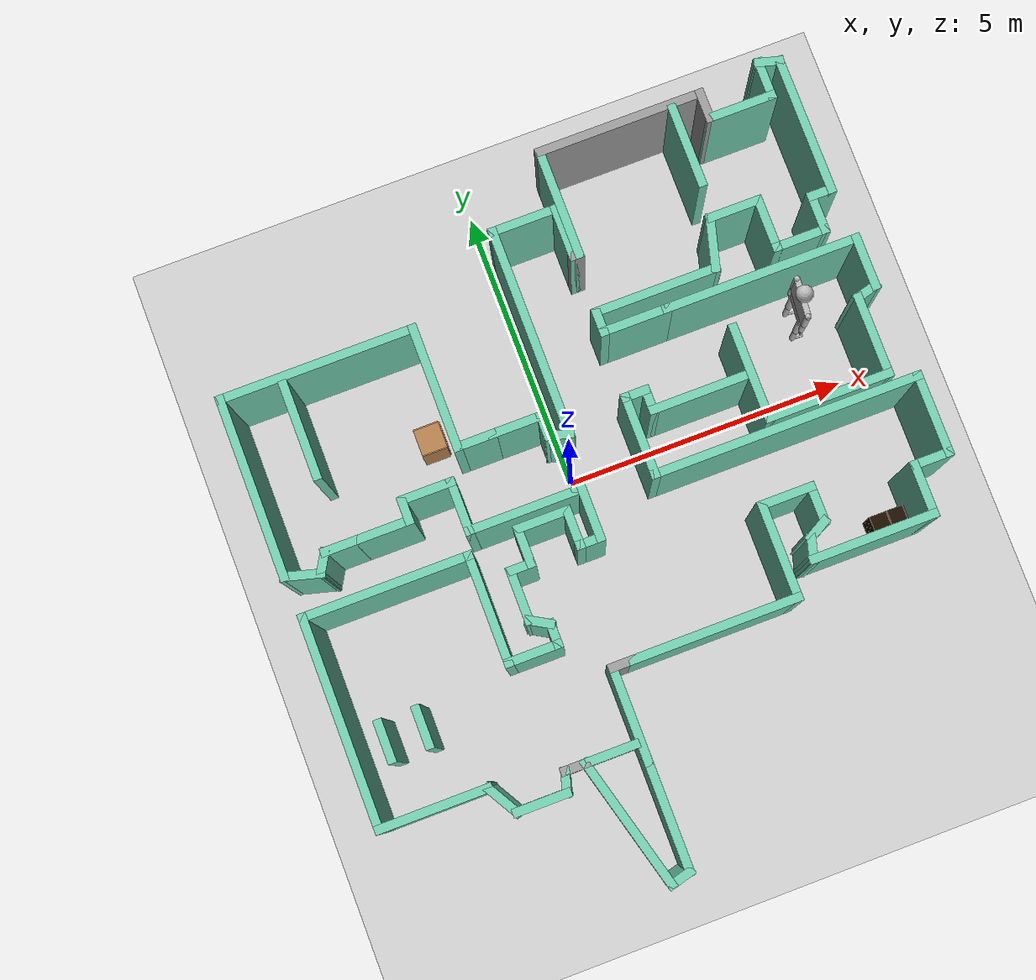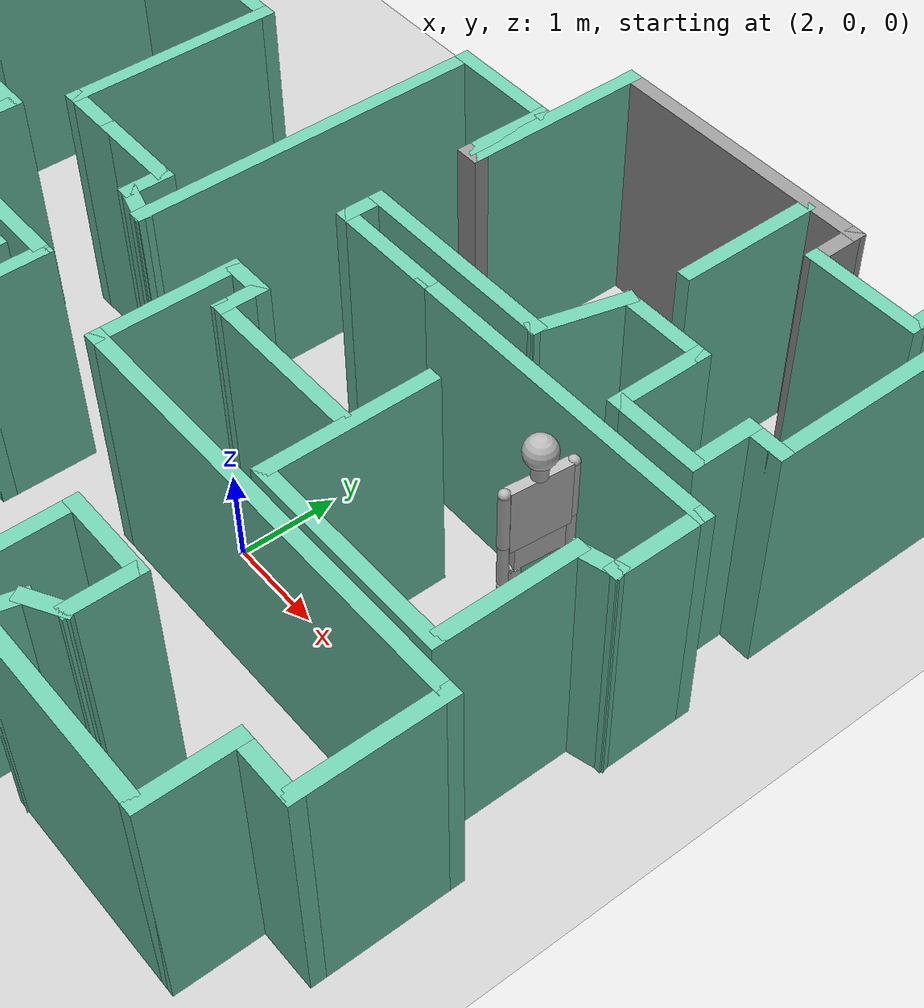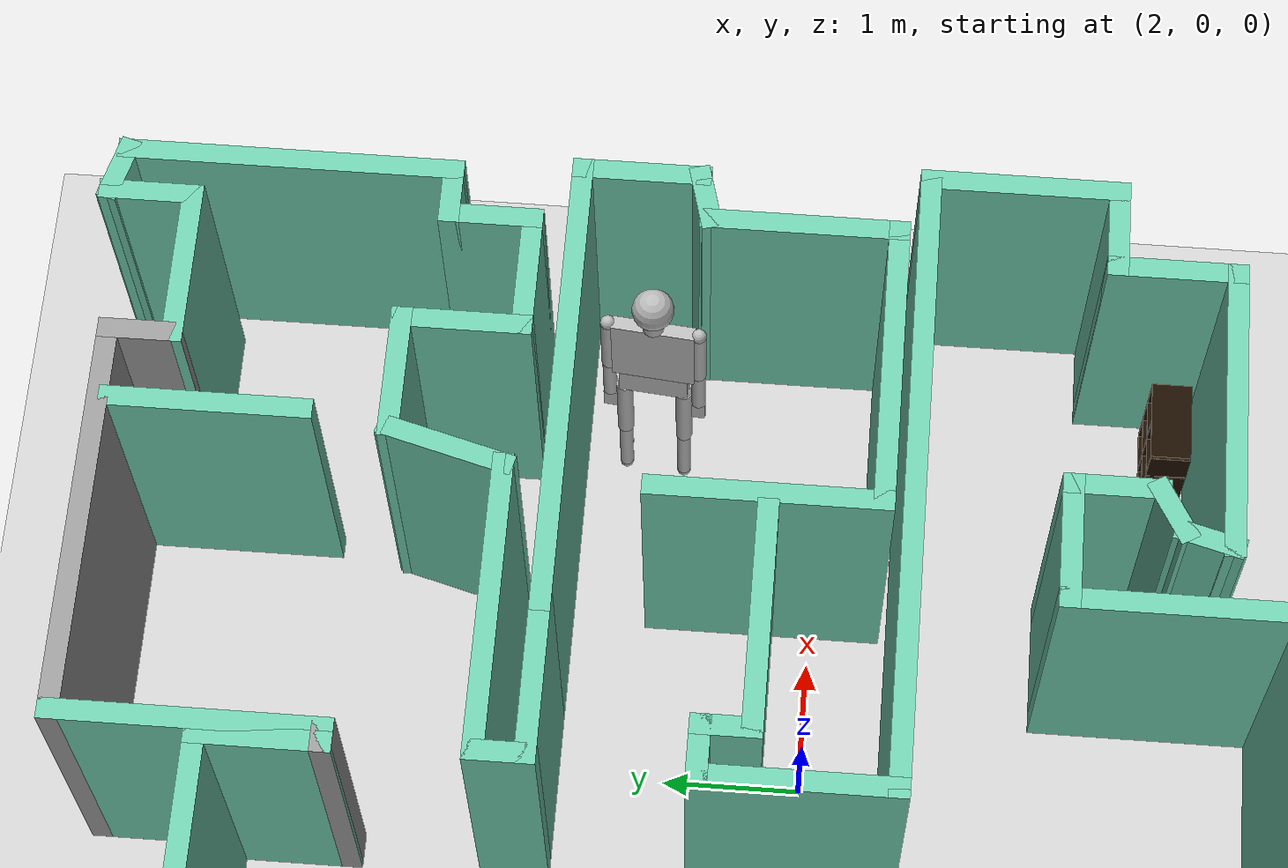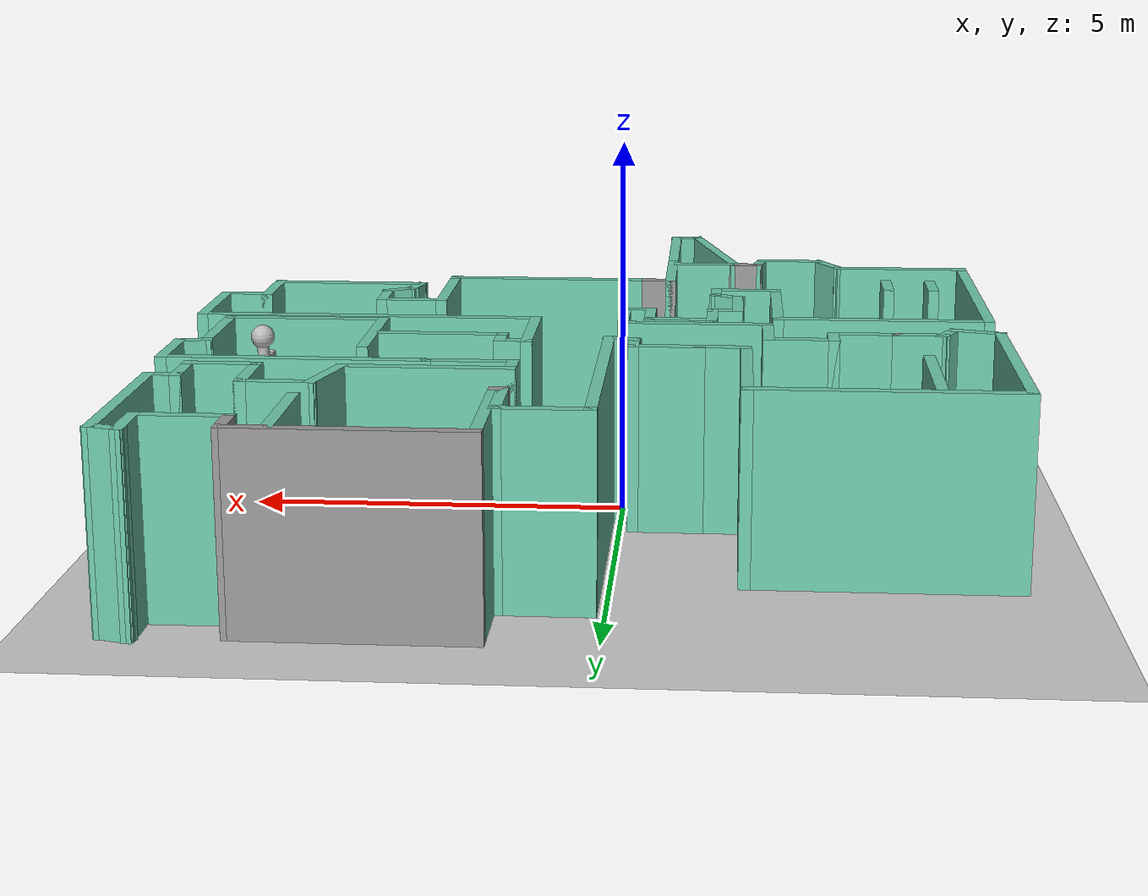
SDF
<sdf version="1.7">
 <world name="default">
  <light name="sun" type="directional">
   <pose>0 0 10 0 -0 0</pose>
   <diffuse>0.8 0.8 0.8 1</diffuse>
   <specular>0.2 0.2 0.2 1</specular>
   <attenuation>
    <range>1000</range>
    <constant>0.9</constant>
    <linear>0.01</linear>
    <quadratic>0.001</quadratic>
   </attenuation>
   <direction>-0.5 0.1 -0.9</direction>
   <spot><inner_angle>0</inner_angle><outer_angle>0</outer_angle><falloff>0</falloff></spot>
  </light>
  <model name="ground_plane">
   <static>1</static>
   <link name="link">
    <collision name="collision">
     <geometry><plane><normal>0 0 1</normal><size>100 100</size></plane></geometry>
     <surface>
      <contact><collide_bitmask>65535</collide_bitmask></contact>
      <friction><ode><mu>100</mu><mu2>50</mu2></ode></friction>
     </surface>
    </collision>
    <visual name="visual">
     <cast_shadows>0</cast_shadows>
     <geometry><plane><normal>0 0 1</normal><size>100 100</size></plane></geometry>
     <material>
      <script><uri>file://media/materials/scripts/gazebo.material</uri><name>Gazebo/Grey</name></script>
     </material>
    </visual>
   </link>
  </model>
  <gravity>0 0 -9.8</gravity>
  <magnetic_field>6e-06 2.3e-05 -4.2e-05</magnetic_field>
  <atmosphere type="adiabatic"/>
  <physics name="default_physics" default="0" type="ode">
   <max_step_size>0.001</max_step_size>
   <real_time_factor>1</real_time_factor>
   <real_time_update_rate>1000</real_time_update_rate>
  </physics>
  <scene><ambient>0.4 0.4 0.4 1</ambient><background>0.7 0.7 0.7 1</background><shadows>1</shadows></scene>
  <audio><device>default</device></audio>
  <spherical_coordinates>
   <surface_model>EARTH_WGS84</surface_model>
   <latitude_deg>0</latitude_deg>
   <longitude_deg>0</longitude_deg>
   <elevation>0</elevation>
   <heading_deg>0</heading_deg>
  </spherical_coordinates>
  <model name="map_5">
   <pose>0.420015 -0.83457 0 0 -0 0</pose>
   <link name="Wall_10">
    <collision name="Wall_10_Collision">
     <geometry><box><size>2 0.15 2.5</size></box></geometry>
     <pose>0 0 1.25 0 -0 0</pose>
    </collision>
    <visual name="Wall_10_Visual">
     <pose>0 0 1.25 0 -0 0</pose>
     <geometry><box><size>2 0.15 2.5</size></box></geometry>
     <material>
      <script><uri>file://media/materials/scripts/gazebo.material</uri><name>Gazebo/Grey</name></script>
      <ambient>0.435294 0.796078 0.67451 1</ambient>
     </material>
     <meta><layer>0</layer></meta>
    </visual>
    <pose>0.946075 4.97016 0 0 -0 -1.5708</pose>
   </link>
   <link name="Wall_100">
    <collision name="Wall_100_Collision">
     <geometry><box><size>1.5 0.15 2.5</size></box></geometry>
     <pose>0 0 1.25 0 -0 0</pose>
    </collision>
    <visual name="Wall_100_Visual">
     <pose>0 0 1.25 0 -0 0</pose>
     <geometry><box><size>1.5 0.15 2.5</size></box></geometry>
     <material>
      <script><uri>file://media/materials/scripts/gazebo.material</uri><name>Gazebo/Grey</name></script>
      <ambient>0.435294 0.796078 0.67451 1</ambient>
     </material>
     <meta><layer>0</layer></meta>
    </visual>
    <pose>3.27534 5.13947 0 0 -0 -1.5708</pose>
   </link>
   <link name="Wall_102">
    <collision name="Wall_102_Collision">
     <geometry><box><size>1.75 0.15 2.5</size></box></geometry>
     <pose>0 0 1.25 0 -0 0</pose>
    </collision>
    <visual name="Wall_102_Visual">
     <pose>0 0 1.25 0 -0 0</pose>
     <geometry><box><size>1.75 0.15 2.5</size></box></geometry>
     <material>
      <script><uri>file://media/materials/scripts/gazebo.material</uri><name>Gazebo/Grey</name></script>
      <ambient>0.435294 0.796078 0.67451 1</ambient>
     </material>
     <meta><layer>0</layer></meta>
    </visual>
    <pose>-4.34162 2.90374 0 0 -0 -1.5708</pose>
   </link>
   <link name="Wall_104">
    <collision name="Wall_104_Collision">
     <geometry><box><size>1 0.15 2.5</size></box></geometry>
     <pose>0 0 1.25 0 -0 0</pose>
    </collision>
    <visual name="Wall_104_Visual">
     <pose>0 0 1.25 0 -0 0</pose>
     <geometry><box><size>1 0.15 2.5</size></box></geometry>
     <material>
      <script><uri>file://media/materials/scripts/gazebo.material</uri><name>Gazebo/Grey</name></script>
      <ambient>0.435294 0.796078 0.67451 1</ambient>
     </material>
     <meta><layer>0</layer></meta>
    </visual>
    <pose>-1.46875 -3.77297 0 0 -0 0</pose>
   </link>
   <link name="Wall_106">
    <collision name="Wall_106_Collision">
     <geometry><box><size>0.75 0.15 2.5</size></box></geometry>
     <pose>0 0 1.25 0 -0 0</pose>
    </collision>
    <visual name="Wall_106_Visual">
     <pose>0 0 1.25 0 -0 0</pose>
     <geometry><box><size>0.75 0.15 2.5</size></box></geometry>
     <material>
      <script><uri>file://media/materials/scripts/gazebo.material</uri><name>Gazebo/Grey</name></script>
      <ambient>0.435294 0.796078 0.67451 1</ambient>
     </material>
     <meta><layer>0</layer></meta>
    </visual>
    <pose>-4.76989 -2.31663 0 0 -0 -1.5708</pose>
   </link>
   <link name="Wall_108">
    <collision name="Wall_108_Collision">
     <geometry><box><size>0.75 0.15 2.5</size></box></geometry>
     <pose>0 0 1.25 0 -0 0</pose>
    </collision>
    <visual name="Wall_108_Visual">
     <pose>0 0 1.25 0 -0 0</pose>
     <geometry><box><size>0.75 0.15 2.5</size></box></geometry>
     <material>
      <script><uri>file://media/materials/scripts/gazebo.material</uri><name>Gazebo/Grey</name></script>
      <ambient>0.435294 0.796078 0.67451 1</ambient>
     </material>
     <meta><layer>0</layer></meta>
    </visual>
    <pose>-4.12749 -2.31663 0 0 -0 -1.5708</pose>
   </link>
   <link name="Wall_11">
    <collision name="Wall_11_Collision">
     <geometry><box><size>0.25 0.15 2.5</size></box></geometry>
     <pose>0 0 1.25 0 -0 0</pose>
    </collision>
    <visual name="Wall_11_Visual">
     <pose>0 0 1.25 0 -0 0</pose>
     <geometry><box><size>0.25 0.15 2.5</size></box></geometry>
     <material>
      <script><uri>file://media/materials/scripts/gazebo.material</uri><name>Gazebo/Grey</name></script>
      <ambient>1 1 1 1</ambient>
     </material>
     <meta><layer>0</layer></meta>
    </visual>
    <pose>0.896075 4.04516 0 0 -0 3.14159</pose>
   </link>
   <link name="Wall_12">
    <collision name="Wall_12_Collision">
     <geometry><box><size>1 0.15 2.5</size></box></geometry>
     <pose>0 0 1.25 0 -0 0</pose>
    </collision>
    <visual name="Wall_12_Visual">
     <pose>0 0 1.25 0 -0 0</pose>
     <geometry><box><size>1 0.15 2.5</size></box></geometry>
     <material>
      <script><uri>file://media/materials/scripts/gazebo.material</uri><name>Gazebo/Grey</name></script>
      <ambient>0.435294 0.796078 0.67451 1</ambient>
     </material>
     <meta><layer>0</layer></meta>
    </visual>
    <pose>0.846075 4.47016 0 0 -0 1.5708</pose>
   </link>
   <link name="Wall_13">
    <collision name="Wall_13_Collision">
     <geometry><box><size>1.25 0.15 2.5</size></box></geometry>
     <pose>0 0 1.25 0 -0 0</pose>
    </collision>
    <visual name="Wall_13_Visual">
     <pose>0 0 1.25 0 -0 0</pose>
     <geometry><box><size>1.25 0.15 2.5</size></box></geometry>
     <material>
      <script><uri>file://media/materials/scripts/gazebo.material</uri><name>Gazebo/Grey</name></script>
      <ambient>0.435294 0.796078 0.67451 1</ambient>
     </material>
     <meta><layer>0</layer></meta>
    </visual>
    <pose>0.296075 4.89516 0 0 -0 3.14159</pose>
   </link>
   <link name="Wall_14">
    <collision name="Wall_14_Collision">
     <geometry><box><size>3.75 0.15 2.5</size></box></geometry>
     <pose>0 0 1.25 0 -0 0</pose>
    </collision>
    <visual name="Wall_14_Visual">
     <pose>0 0 1.25 0 -0 0</pose>
     <geometry><box><size>3.75 0.15 2.5</size></box></geometry>
     <material>
      <script><uri>file://media/materials/scripts/gazebo.material</uri><name>Gazebo/Grey</name></script>
      <ambient>0.435294 0.796078 0.67451 1</ambient>
     </material>
     <meta><layer>0</layer></meta>
    </visual>
    <pose>-0.253925 3.09516 0 0 -0 -1.5708</pose>
   </link>
   <link name="Wall_15">
    <collision name="Wall_15_Collision">
     <geometry><box><size>0.5 0.15 2.5</size></box></geometry>
     <pose>0 0 1.25 0 -0 0</pose>
    </collision>
    <visual name="Wall_15_Visual">
     <pose>0 0 1.25 0 -0 0</pose>
     <geometry><box><size>0.5 0.15 2.5</size></box></geometry>
     <material>
      <script><uri>file://media/materials/scripts/gazebo.material</uri><name>Gazebo/Grey</name></script>
      <ambient>0.435294 0.796078 0.67451 1</ambient>
     </material>
     <meta><layer>0</layer></meta>
    </visual>
    <pose>-0.422962 1.34046 0 0 -0 2.87979</pose>
   </link>
   <link name="Wall_16">
    <collision name="Wall_16_Collision">
     <geometry><box><size>0.5 0.15 2.5</size></box></geometry>
     <pose>0 0 1.25 0 -0 0</pose>
    </collision>
    <visual name="Wall_16_Visual">
     <pose>0 0 1.25 0 -0 0</pose>
     <geometry><box><size>0.5 0.15 2.5</size></box></geometry>
     <material>
      <script><uri>file://media/materials/scripts/gazebo.material</uri><name>Gazebo/Grey</name></script>
      <ambient>0.435294 0.796078 0.67451 1</ambient>
     </material>
     <meta><layer>0</layer></meta>
    </visual>
    <pose>-0.591999 1.56075 0 0 -0 1.5708</pose>
   </link>
   <link name="Wall_17">
    <collision name="Wall_17_Collision">
     <geometry><box><size>1 0.15 2.5</size></box></geometry>
     <pose>0 0 1.25 0 -0 0</pose>
    </collision>
    <visual name="Wall_17_Visual">
     <pose>0 0 1.25 0 -0 0</pose>
     <geometry><box><size>1 0.15 2.5</size></box></geometry>
     <material>
      <script><uri>file://media/materials/scripts/gazebo.material</uri><name>Gazebo/Grey</name></script>
      <ambient>0.435294 0.796078 0.67451 1</ambient>
     </material>
     <meta><layer>0</layer></meta>
    </visual>
    <pose>-1.017 1.73575 0 0 -0 3.14159</pose>
   </link>
   <link name="Wall_18">
    <collision name="Wall_18_Collision">
     <geometry><box><size>0.75 0.15 2.5</size></box></geometry>
     <pose>0 0 1.25 0 -0 0</pose>
    </collision>
    <visual name="Wall_18_Visual">
     <pose>0 0 1.25 0 -0 0</pose>
     <geometry><box><size>0.75 0.15 2.5</size></box></geometry>
     <material>
      <script><uri>file://media/materials/scripts/gazebo.material</uri><name>Gazebo/Grey</name></script>
      <ambient>0.435294 0.796078 0.67451 1</ambient>
     </material>
     <meta><layer>0</layer></meta>
    </visual>
    <pose>-1.742 1.73575 0 0 -0 3.14159</pose>
   </link>
   <link name="Wall_19">
    <collision name="Wall_19_Collision">
     <geometry><box><size>2.25 0.15 2.5</size></box></geometry>
     <pose>0 0 1.25 0 -0 0</pose>
    </collision>
    <visual name="Wall_19_Visual">
     <pose>0 0 1.25 0 -0 0</pose>
     <geometry><box><size>2.25 0.15 2.5</size></box></geometry>
     <material>
      <script><uri>file://media/materials/scripts/gazebo.material</uri><name>Gazebo/Grey</name></script>
      <ambient>0.435294 0.796078 0.67451 1</ambient>
     </material>
     <meta><layer>0</layer></meta>
    </visual>
    <pose>-2.042 2.78575 0 0 -0 1.5708</pose>
   </link>
   <link name="Wall_20">
    <collision name="Wall_20_Collision">
     <geometry><box><size>3.5 0.15 2.5</size></box></geometry>
     <pose>0 0 1.25 0 -0 0</pose>
    </collision>
    <visual name="Wall_20_Visual">
     <pose>0 0 1.25 0 -0 0</pose>
     <geometry><box><size>3.5 0.15 2.5</size></box></geometry>
     <material>
      <script><uri>file://media/materials/scripts/gazebo.material</uri><name>Gazebo/Grey</name></script>
      <ambient>0.435294 0.796078 0.67451 1</ambient>
     </material>
     <meta><layer>0</layer></meta>
    </visual>
    <pose>-3.717 3.83575 0 0 -0 3.14159</pose>
   </link>
   <link name="Wall_21">
    <collision name="Wall_21_Collision">
     <geometry><box><size>3.25 0.15 2.5</size></box></geometry>
     <pose>0 0 1.25 0 -0 0</pose>
    </collision>
    <visual name="Wall_21_Visual">
     <pose>0 0 1.25 0 -0 0</pose>
     <geometry><box><size>3.25 0.15 2.5</size></box></geometry>
     <material>
      <script><uri>file://media/materials/scripts/gazebo.material</uri><name>Gazebo/Grey</name></script>
      <ambient>0.435294 0.796078 0.67451 1</ambient>
     </material>
     <meta><layer>0</layer></meta>
    </visual>
    <pose>-5.392 2.28575 0 0 -0 -1.5708</pose>
   </link>
   <link name="Wall_22">
    <collision name="Wall_22_Collision">
     <geometry><box><size>0.75 0.15 2.5</size></box></geometry>
     <pose>0 0 1.25 0 -0 0</pose>
    </collision>
    <visual name="Wall_22_Visual">
     <pose>0 0 1.25 0 -0 0</pose>
     <geometry><box><size>0.75 0.15 2.5</size></box></geometry>
     <material>
      <script><uri>file://media/materials/scripts/gazebo.material</uri><name>Gazebo/Grey</name></script>
      <ambient>0.435294 0.796078 0.67451 1</ambient>
     </material>
     <meta><layer>0</layer></meta>
    </visual>
    <pose>-5.10222 0.658104 0 0 -0 -0.261799</pose>
   </link>
   <link name="Wall_23">
    <collision name="Wall_23_Collision">
     <geometry><box><size>0.5 0.15 2.5</size></box></geometry>
     <pose>0 0 1.25 0 -0 0</pose>
    </collision>
    <visual name="Wall_23_Visual">
     <pose>0 0 1.25 0 -0 0</pose>
     <geometry><box><size>0.5 0.15 2.5</size></box></geometry>
     <material>
      <script><uri>file://media/materials/scripts/gazebo.material</uri><name>Gazebo/Grey</name></script>
      <ambient>0.435294 0.796078 0.67451 1</ambient>
     </material>
     <meta><layer>0</layer></meta>
    </visual>
    <pose>-4.72494 0.732012 0 0 -0 1.0472</pose>
   </link>
   <link name="Wall_24">
    <collision name="Wall_24_Collision">
     <geometry><box><size>0.75 0.15 2.5</size></box></geometry>
     <pose>0 0 1.25 0 -0 0</pose>
    </collision>
    <visual name="Wall_24_Visual">
     <pose>0 0 1.25 0 -0 0</pose>
     <geometry><box><size>0.75 0.15 2.5</size></box></geometry>
     <material>
      <script><uri>file://media/materials/scripts/gazebo.material</uri><name>Gazebo/Grey</name></script>
      <ambient>0.435294 0.796078 0.67451 1</ambient>
     </material>
     <meta><layer>0</layer></meta>
    </visual>
    <pose>-4.33744 0.883567 0 0 -0 0</pose>
   </link>
   <link name="Wall_25">
    <collision name="Wall_25_Collision">
     <geometry><box><size>0.15 0.15 2.5</size></box></geometry>
     <pose>0 0 1.25 0 -0 0</pose>
    </collision>
    <visual name="Wall_25_Visual">
     <pose>0 0 1.25 0 -0 0</pose>
     <geometry><box><size>0.15 0.15 2.5</size></box></geometry>
     <material>
      <script><uri>file://media/materials/scripts/gazebo.material</uri><name>Gazebo/Grey</name></script>
      <ambient>1 1 1 1</ambient>
     </material>
     <meta><layer>0</layer></meta>
    </visual>
    <pose>-4.03744 0.883567 0 0 -0 0</pose>
   </link>
   <link name="Wall_26">
    <collision name="Wall_26_Collision">
     <geometry><box><size>1 0.15 2.5</size></box></geometry>
     <pose>0 0 1.25 0 -0 0</pose>
    </collision>
    <visual name="Wall_26_Visual">
     <pose>0 0 1.25 0 -0 0</pose>
     <geometry><box><size>1 0.15 2.5</size></box></geometry>
     <material>
      <script><uri>file://media/materials/scripts/gazebo.material</uri><name>Gazebo/Grey</name></script>
      <ambient>0.435294 0.796078 0.67451 1</ambient>
     </material>
     <meta><layer>0</layer></meta>
    </visual>
    <pose>-3.61244 0.883567 0 0 -0 0</pose>
   </link>
   <link name="Wall_27">
    <collision name="Wall_27_Collision">
     <geometry><box><size>0.5 0.15 2.5</size></box></geometry>
     <pose>0 0 1.25 0 -0 0</pose>
    </collision>
    <visual name="Wall_27_Visual">
     <pose>0 0 1.25 0 -0 0</pose>
     <geometry><box><size>0.5 0.15 2.5</size></box></geometry>
     <material>
      <script><uri>file://media/materials/scripts/gazebo.material</uri><name>Gazebo/Grey</name></script>
      <ambient>0.435294 0.796078 0.67451 1</ambient>
     </material>
     <meta><layer>0</layer></meta>
    </visual>
    <pose>-3.18744 1.05857 0 0 -0 1.5708</pose>
   </link>
   <link name="Wall_28">
    <collision name="Wall_28_Collision">
     <geometry><box><size>1 0.15 2.5</size></box></geometry>
     <pose>0 0 1.25 0 -0 0</pose>
    </collision>
    <visual name="Wall_28_Visual">
     <pose>0 0 1.25 0 -0 0</pose>
     <geometry><box><size>1 0.15 2.5</size></box></geometry>
     <material>
      <script><uri>file://media/materials/scripts/gazebo.material</uri><name>Gazebo/Grey</name></script>
      <ambient>0.435294 0.796078 0.67451 1</ambient>
     </material>
     <meta><layer>0</layer></meta>
    </visual>
    <pose>-2.76244 1.23357 0 0 -0 0</pose>
   </link>
   <link name="Wall_29">
    <collision name="Wall_29_Collision">
     <geometry><box><size>1 0.15 2.5</size></box></geometry>
     <pose>0 0 1.25 0 -0 0</pose>
    </collision>
    <visual name="Wall_29_Visual">
     <pose>0 0 1.25 0 -0 0</pose>
     <geometry><box><size>1 0.15 2.5</size></box></geometry>
     <material>
      <script><uri>file://media/materials/scripts/gazebo.material</uri><name>Gazebo/Grey</name></script>
      <ambient>0.435294 0.796078 0.67451 1</ambient>
     </material>
     <meta><layer>0</layer></meta>
    </visual>
    <pose>-2.33744 0.808567 0 0 -0 -1.5708</pose>
   </link>
   <link name="Wall_30">
    <collision name="Wall_30_Collision">
     <geometry><box><size>2 0.15 2.5</size></box></geometry>
     <pose>0 0 1.25 0 -0 0</pose>
    </collision>
    <visual name="Wall_30_Visual">
     <pose>0 0 1.25 0 -0 0</pose>
     <geometry><box><size>2 0.15 2.5</size></box></geometry>
     <material>
      <script><uri>file://media/materials/scripts/gazebo.material</uri><name>Gazebo/Grey</name></script>
      <ambient>0.435294 0.796078 0.67451 1</ambient>
     </material>
     <meta><layer>0</layer></meta>
    </visual>
    <pose>-1.41244 0.383567 0 0 -0 0</pose>
   </link>
   <link name="Wall_32">
    <collision name="Wall_32_Collision">
     <geometry><box><size>0.25 0.15 2.5</size></box></geometry>
     <pose>0 0 1.25 0 -0 0</pose>
    </collision>
    <visual name="Wall_32_Visual">
     <pose>0 0 1.25 0 -0 0</pose>
     <geometry><box><size>0.25 0.15 2.5</size></box></geometry>
     <material>
      <script><uri>file://media/materials/scripts/gazebo.material</uri><name>Gazebo/Grey</name></script>
      <ambient>0.435294 0.796078 0.67451 1</ambient>
     </material>
     <meta><layer>0</layer></meta>
    </visual>
    <pose>-0.437444 0.383567 0 0 -0 0</pose>
   </link>
   <link name="Wall_33">
    <collision name="Wall_33_Collision">
     <geometry><box><size>1 0.15 2.5</size></box></geometry>
     <pose>0 0 1.25 0 -0 0</pose>
    </collision>
    <visual name="Wall_33_Visual">
     <pose>0 0 1.25 0 -0 0</pose>
     <geometry><box><size>1 0.15 2.5</size></box></geometry>
     <material>
      <script><uri>file://media/materials/scripts/gazebo.material</uri><name>Gazebo/Grey</name></script>
      <ambient>0.435294 0.796078 0.67451 1</ambient>
     </material>
     <meta><layer>0</layer></meta>
    </visual>
    <pose>-0.387444 -0.041433 0 0 -0 -1.5708</pose>
   </link>
   <link name="Wall_34">
    <collision name="Wall_34_Collision">
     <geometry><box><size>0.5 0.15 2.5</size></box></geometry>
     <pose>0 0 1.25 0 -0 0</pose>
    </collision>
    <visual name="Wall_34_Visual">
     <pose>0 0 1.25 0 -0 0</pose>
     <geometry><box><size>0.5 0.15 2.5</size></box></geometry>
     <material>
      <script><uri>file://media/materials/scripts/gazebo.material</uri><name>Gazebo/Grey</name></script>
      <ambient>0.435294 0.796078 0.67451 1</ambient>
     </material>
     <meta><layer>0</layer></meta>
    </visual>
    <pose>-0.562444 -0.466433 0 0 -0 3.14159</pose>
   </link>
   <link name="Wall_35">
    <collision name="Wall_35_Collision">
     <geometry><box><size>0.75 0.15 2.5</size></box></geometry>
     <pose>0 0 1.25 0 -0 0</pose>
    </collision>
    <visual name="Wall_35_Visual">
     <pose>0 0 1.25 0 -0 0</pose>
     <geometry><box><size>0.75 0.15 2.5</size></box></geometry>
     <material>
      <script><uri>file://media/materials/scripts/gazebo.material</uri><name>Gazebo/Grey</name></script>
      <ambient>0.435294 0.796078 0.67451 1</ambient>
     </material>
     <meta><layer>0</layer></meta>
    </visual>
    <pose>-0.737444 -0.166433 0 0 -0 1.5708</pose>
   </link>
   <link name="Wall_36">
    <collision name="Wall_36_Collision">
     <geometry><box><size>1 0.15 2.5</size></box></geometry>
     <pose>0 0 1.25 0 -0 0</pose>
    </collision>
    <visual name="Wall_36_Visual">
     <pose>0 0 1.25 0 -0 0</pose>
     <geometry><box><size>1 0.15 2.5</size></box></geometry>
     <material>
      <script><uri>file://media/materials/scripts/gazebo.material</uri><name>Gazebo/Grey</name></script>
      <ambient>0.435294 0.796078 0.67451 1</ambient>
     </material>
     <meta><layer>0</layer></meta>
    </visual>
    <pose>-1.16244 0.133567 0 0 -0 3.14159</pose>
   </link>
   <link name="Wall_37">
    <collision name="Wall_37_Collision">
     <geometry><box><size>0.75 0.15 2.5</size></box></geometry>
     <pose>0 0 1.25 0 -0 0</pose>
    </collision>
    <visual name="Wall_37_Visual">
     <pose>0 0 1.25 0 -0 0</pose>
     <geometry><box><size>0.75 0.15 2.5</size></box></geometry>
     <material>
      <script><uri>file://media/materials/scripts/gazebo.material</uri><name>Gazebo/Grey</name></script>
      <ambient>0.435294 0.796078 0.67451 1</ambient>
     </material>
     <meta><layer>0</layer></meta>
    </visual>
    <pose>-1.58744 -0.166433 0 0 -0 -1.5708</pose>
   </link>
   <link name="Wall_38">
    <collision name="Wall_38_Collision">
     <geometry><box><size>0.5 0.15 2.5</size></box></geometry>
     <pose>0 0 1.25 0 -0 0</pose>
    </collision>
    <visual name="Wall_38_Visual">
     <pose>0 0 1.25 0 -0 0</pose>
     <geometry><box><size>0.5 0.15 2.5</size></box></geometry>
     <material>
      <script><uri>file://media/materials/scripts/gazebo.material</uri><name>Gazebo/Grey</name></script>
      <ambient>0.435294 0.796078 0.67451 1</ambient>
     </material>
     <meta><layer>0</layer></meta>
    </visual>
    <pose>-1.76244 -0.466433 0 0 -0 3.14159</pose>
   </link>
   <link name="Wall_39">
    <collision name="Wall_39_Collision">
     <geometry><box><size>1 0.15 2.5</size></box></geometry>
     <pose>0 0 1.25 0 -0 0</pose>
    </collision>
    <visual name="Wall_39_Visual">
     <pose>0 0 1.25 0 -0 0</pose>
     <geometry><box><size>1 0.15 2.5</size></box></geometry>
     <material>
      <script><uri>file://media/materials/scripts/gazebo.material</uri><name>Gazebo/Grey</name></script>
      <ambient>0.435294 0.796078 0.67451 1</ambient>
     </material>
     <meta><layer>0</layer></meta>
    </visual>
    <pose>-1.93744 -0.891433 0 0 -0 -1.5708</pose>
   </link>
   <link name="Wall_40">
    <collision name="Wall_40_Collision">
     <geometry><box><size>0.5 0.15 2.5</size></box></geometry>
     <pose>0 0 1.25 0 -0 0</pose>
    </collision>
    <visual name="Wall_40_Visual">
     <pose>0 0 1.25 0 -0 0</pose>
     <geometry><box><size>0.5 0.15 2.5</size></box></geometry>
     <material>
      <script><uri>file://media/materials/scripts/gazebo.material</uri><name>Gazebo/Grey</name></script>
      <ambient>0.435294 0.796078 0.67451 1</ambient>
     </material>
     <meta><layer>0</layer></meta>
    </visual>
    <pose>-1.78589 -1.40393 0 0 -0 -0.523599</pose>
   </link>
   <link name="Wall_41">
    <collision name="Wall_41_Collision">
     <geometry><box><size>0.5 0.15 2.5</size></box></geometry>
     <pose>0 0 1.25 0 -0 0</pose>
    </collision>
    <visual name="Wall_41_Visual">
     <pose>0 0 1.25 0 -0 0</pose>
     <geometry><box><size>0.5 0.15 2.5</size></box></geometry>
     <material>
      <script><uri>file://media/materials/scripts/gazebo.material</uri><name>Gazebo/Grey</name></script>
      <ambient>0.435294 0.796078 0.67451 1</ambient>
     </material>
     <meta><layer>0</layer></meta>
    </visual>
    <pose>-1.63434 -1.66643 0 0 -0 -1.5708</pose>
   </link>
   <link name="Wall_42">
    <collision name="Wall_42_Collision">
     <geometry><box><size>1 0.15 2.5</size></box></geometry>
     <pose>0 0 1.25 0 -0 0</pose>
    </collision>
    <visual name="Wall_42_Visual">
     <pose>0 0 1.25 0 -0 0</pose>
     <geometry><box><size>1 0.15 2.5</size></box></geometry>
     <material>
      <script><uri>file://media/materials/scripts/gazebo.material</uri><name>Gazebo/Grey</name></script>
      <ambient>0.435294 0.796078 0.67451 1</ambient>
     </material>
     <meta><layer>0</layer></meta>
    </visual>
    <pose>-2.05933 -1.84143 0 0 -0 3.14159</pose>
   </link>
   <link name="Wall_43">
    <collision name="Wall_43_Collision">
     <geometry><box><size>2 0.15 2.5</size></box></geometry>
     <pose>0 0 1.25 0 -0 0</pose>
    </collision>
    <visual name="Wall_43_Visual">
     <pose>0 0 1.25 0 -0 0</pose>
     <geometry><box><size>2 0.15 2.5</size></box></geometry>
     <material>
      <script><uri>file://media/materials/scripts/gazebo.material</uri><name>Gazebo/Grey</name></script>
      <ambient>0.435294 0.796078 0.67451 1</ambient>
     </material>
     <meta><layer>0</layer></meta>
    </visual>
    <pose>-2.48434 -0.916433 0 0 -0 1.5708</pose>
   </link>
   <link name="Wall_44">
    <collision name="Wall_44_Collision">
     <geometry><box><size>3 0.15 2.5</size></box></geometry>
     <pose>0 0 1.25 0 -0 0</pose>
    </collision>
    <visual name="Wall_44_Visual">
     <pose>0 0 1.25 0 -0 0</pose>
     <geometry><box><size>3 0.15 2.5</size></box></geometry>
     <material>
      <script><uri>file://media/materials/scripts/gazebo.material</uri><name>Gazebo/Grey</name></script>
      <ambient>0.435294 0.796078 0.67451 1</ambient>
     </material>
     <meta><layer>0</layer></meta>
    </visual>
    <pose>-3.90934 0.008567 0 0 -0 3.14159</pose>
   </link>
   <link name="Wall_45">
    <collision name="Wall_45_Collision">
     <geometry><box><size>3.75 0.15 2.5</size></box></geometry>
     <pose>0 0 1.25 0 -0 0</pose>
    </collision>
    <visual name="Wall_45_Visual">
     <pose>0 0 1.25 0 -0 0</pose>
     <geometry><box><size>3.75 0.15 2.5</size></box></geometry>
     <material>
      <script><uri>file://media/materials/scripts/gazebo.material</uri><name>Gazebo/Grey</name></script>
      <ambient>0.435294 0.796078 0.67451 1</ambient>
     </material>
     <meta><layer>0</layer></meta>
    </visual>
    <pose>-5.33434 -1.79143 0 0 -0 -1.5708</pose>
   </link>
   <link name="Wall_46">
    <collision name="Wall_46_Collision">
     <geometry><box><size>2 0.15 2.5</size></box></geometry>
     <pose>0 0 1.25 0 -0 0</pose>
    </collision>
    <visual name="Wall_46_Visual">
     <pose>0 0 1.25 0 -0 0</pose>
     <geometry><box><size>2 0.15 2.5</size></box></geometry>
     <material>
      <script><uri>file://media/materials/scripts/gazebo.material</uri><name>Gazebo/Grey</name></script>
      <ambient>0.435294 0.796078 0.67451 1</ambient>
     </material>
     <meta><layer>0</layer></meta>
    </visual>
    <pose>-4.40933 -3.59143 0 0 -0 0</pose>
   </link>
   <link name="Wall_47">
    <collision name="Wall_47_Collision">
     <geometry><box><size>0.75 0.15 2.5</size></box></geometry>
     <pose>0 0 1.25 0 -0 0</pose>
    </collision>
    <visual name="Wall_47_Visual">
     <pose>0 0 1.25 0 -0 0</pose>
     <geometry><box><size>0.75 0.15 2.5</size></box></geometry>
     <material>
      <script><uri>file://media/materials/scripts/gazebo.material</uri><name>Gazebo/Grey</name></script>
      <ambient>0.435294 0.796078 0.67451 1</ambient>
     </material>
     <meta><layer>0</layer></meta>
    </visual>
    <pose>-3.33433 -3.85124 0 0 -0 -1.0472</pose>
   </link>
   <link name="Wall_48">
    <collision name="Wall_48_Collision">
     <geometry><box><size>1 0.15 2.5</size></box></geometry>
     <pose>0 0 1.25 0 -0 0</pose>
    </collision>
    <visual name="Wall_48_Visual">
     <pose>0 0 1.25 0 -0 0</pose>
     <geometry><box><size>1 0.15 2.5</size></box></geometry>
     <material>
      <script><uri>file://media/materials/scripts/gazebo.material</uri><name>Gazebo/Grey</name></script>
      <ambient>0.435294 0.796078 0.67451 1</ambient>
     </material>
     <meta><layer>0</layer></meta>
    </visual>
    <pose>-2.75934 -4.11105 0 0 -0 0</pose>
   </link>
   <link name="Wall_49">
    <collision name="Wall_49_Collision">
     <geometry><box><size>0.5 0.15 2.5</size></box></geometry>
     <pose>0 0 1.25 0 -0 0</pose>
    </collision>
    <visual name="Wall_49_Visual">
     <pose>0 0 1.25 0 -0 0</pose>
     <geometry><box><size>0.5 0.15 2.5</size></box></geometry>
     <material>
      <script><uri>file://media/materials/scripts/gazebo.material</uri><name>Gazebo/Grey</name></script>
      <ambient>0.435294 0.796078 0.67451 1</ambient>
     </material>
     <meta><layer>0</layer></meta>
    </visual>
    <pose>-2.28904 -3.94201 0 0 -0 1.309</pose>
   </link>
   <link name="Wall_50">
    <collision name="Wall_50_Collision">
     <geometry><box><size>0.5 0.15 2.5</size></box></geometry>
     <pose>0 0 1.25 0 -0 0</pose>
    </collision>
    <visual name="Wall_50_Visual">
     <pose>0 0 1.25 0 -0 0</pose>
     <geometry><box><size>0.5 0.15 2.5</size></box></geometry>
     <material>
      <script><uri>file://media/materials/scripts/gazebo.material</uri><name>Gazebo/Grey</name></script>
      <ambient>1 1 1 1</ambient>
     </material>
     <meta><layer>0</layer></meta>
    </visual>
    <pose>-2.06875 -3.77297 0 0 -0 0</pose>
   </link>
   <link name="Wall_51">
    <collision name="Wall_51_Collision">
     <geometry><box><size>2.5 0.15 2.5</size></box></geometry>
     <pose>0 0 1.25 0 -0 0</pose>
    </collision>
    <visual name="Wall_51_Visual">
     <pose>0 0 1.25 0 -0 0</pose>
     <geometry><box><size>2.5 0.15 2.5</size></box></geometry>
     <material>
      <script><uri>file://media/materials/scripts/gazebo.material</uri><name>Gazebo/Grey</name></script>
      <ambient>0.435294 0.796078 0.67451 1</ambient>
     </material>
     <meta><layer>0</layer></meta>
    </visual>
    <pose>-1.58964 -4.90794 0 0 -0 -1.309</pose>
   </link>
   <link name="Wall_52">
    <collision name="Wall_52_Collision">
     <geometry><box><size>0.5 0.15 2.5</size></box></geometry>
     <pose>0 0 1.25 0 -0 0</pose>
    </collision>
    <visual name="Wall_52_Visual">
     <pose>0 0 1.25 0 -0 0</pose>
     <geometry><box><size>0.5 0.15 2.5</size></box></geometry>
     <material>
      <script><uri>file://media/materials/scripts/gazebo.material</uri><name>Gazebo/Grey</name></script>
      <ambient>0.435294 0.796078 0.67451 1</ambient>
     </material>
     <meta><layer>0</layer></meta>
    </visual>
    <pose>-1.11649 -5.99761 0 0 -0 0.261799</pose>
   </link>
   <link name="Wall_53">
    <collision name="Wall_53_Collision">
     <geometry><box><size>2 0.15 2.5</size></box></geometry>
     <pose>0 0 1.25 0 -0 0</pose>
    </collision>
    <visual name="Wall_53_Visual">
     <pose>0 0 1.25 0 -0 0</pose>
     <geometry><box><size>2 0.15 2.5</size></box></geometry>
     <material>
      <script><uri>file://media/materials/scripts/gazebo.material</uri><name>Gazebo/Grey</name></script>
      <ambient>0.435294 0.796078 0.67451 1</ambient>
     </material>
     <meta><layer>0</layer></meta>
    </visual>
    <pose>-0.947449 -5.02731 0 0 -0 1.5708</pose>
   </link>
   <link name="Wall_54">
    <collision name="Wall_54_Collision">
     <geometry><box><size>1.75 0.15 2.5</size></box></geometry>
     <pose>0 0 1.25 0 -0 0</pose>
    </collision>
    <visual name="Wall_54_Visual">
     <pose>0 0 1.25 0 -0 0</pose>
     <geometry><box><size>1.75 0.15 2.5</size></box></geometry>
     <material>
      <script><uri>file://media/materials/scripts/gazebo.material</uri><name>Gazebo/Grey</name></script>
      <ambient>0.435294 0.796078 0.67451 1</ambient>
     </material>
     <meta><layer>0</layer></meta>
    </visual>
    <pose>-0.947449 -3.30231 0 0 -0 1.5708</pose>
   </link>
   <link name="Wall_55">
    <collision name="Wall_55_Collision">
     <geometry><box><size>0.5 0.15 2.5</size></box></geometry>
     <pose>0 0 1.25 0 -0 0</pose>
    </collision>
    <visual name="Wall_55_Visual">
     <pose>0 0 1.25 0 -0 0</pose>
     <geometry><box><size>0.5 0.15 2.5</size></box></geometry>
     <material>
      <script><uri>file://media/materials/scripts/gazebo.material</uri><name>Gazebo/Grey</name></script>
      <ambient>1 1 1 1</ambient>
     </material>
     <meta><layer>0</layer></meta>
    </visual>
    <pose>-0.772449 -2.50231 0 0 -0 0</pose>
   </link>
   <link name="Wall_56">
    <collision name="Wall_56_Collision">
     <geometry><box><size>3 0.15 2.5</size></box></geometry>
     <pose>0 0 1.25 0 -0 0</pose>
    </collision>
    <visual name="Wall_56_Visual">
     <pose>0 0 1.25 0 -0 0</pose>
     <geometry><box><size>3 0.15 2.5</size></box></geometry>
     <material>
      <script><uri>file://media/materials/scripts/gazebo.material</uri><name>Gazebo/Grey</name></script>
      <ambient>0.435294 0.796078 0.67451 1</ambient>
     </material>
     <meta><layer>0</layer></meta>
    </visual>
    <pose>0.827551 -2.50231 0 0 -0 0</pose>
   </link>
   <link name="Wall_57">
    <collision name="Wall_57_Collision">
     <geometry><box><size>1.75 0.15 2.5</size></box></geometry>
     <pose>0 0 1.25 0 -0 0</pose>
    </collision>
    <visual name="Wall_57_Visual">
     <pose>0 0 1.25 0 -0 0</pose>
     <geometry><box><size>1.75 0.15 2.5</size></box></geometry>
     <material>
      <script><uri>file://media/materials/scripts/gazebo.material</uri><name>Gazebo/Grey</name></script>
      <ambient>0.435294 0.796078 0.67451 1</ambient>
     </material>
     <meta><layer>0</layer></meta>
    </visual>
    <pose>2.25255 -1.70231 0 0 -0 1.5708</pose>
   </link>
   <link name="Wall_58">
    <collision name="Wall_58_Collision">
     <geometry><box><size>1 0.15 2.5</size></box></geometry>
     <pose>0 0 1.25 0 -0 0</pose>
    </collision>
    <visual name="Wall_58_Visual">
     <pose>0 0 1.25 0 -0 0</pose>
     <geometry><box><size>1 0.15 2.5</size></box></geometry>
     <material>
      <script><uri>file://media/materials/scripts/gazebo.material</uri><name>Gazebo/Grey</name></script>
      <ambient>0.435294 0.796078 0.67451 1</ambient>
     </material>
     <meta><layer>0</layer></meta>
    </visual>
    <pose>2.67755 -0.902313 0 0 -0 0</pose>
   </link>
   <link name="Wall_59">
    <collision name="Wall_59_Collision">
     <geometry><box><size>0.75 0.15 2.5</size></box></geometry>
     <pose>0 0 1.25 0 -0 0</pose>
    </collision>
    <visual name="Wall_59_Visual">
     <pose>0 0 1.25 0 -0 0</pose>
     <geometry><box><size>0.75 0.15 2.5</size></box></geometry>
     <material>
      <script><uri>file://media/materials/scripts/gazebo.material</uri><name>Gazebo/Grey</name></script>
      <ambient>0.435294 0.796078 0.67451 1</ambient>
     </material>
     <meta><layer>0</layer></meta>
    </visual>
    <pose>3.10255 -1.20231 0 0 -0 -1.5708</pose>
   </link>
   <link name="Wall_60">
    <collision name="Wall_60_Collision">
     <geometry><box><size>0.5 0.15 2.5</size></box></geometry>
     <pose>0 0 1.25 0 -0 0</pose>
    </collision>
    <visual name="Wall_60_Visual">
     <pose>0 0 1.25 0 -0 0</pose>
     <geometry><box><size>0.5 0.15 2.5</size></box></geometry>
     <material>
      <script><uri>file://media/materials/scripts/gazebo.material</uri><name>Gazebo/Grey</name></script>
      <ambient>0.435294 0.796078 0.67451 1</ambient>
     </material>
     <meta><layer>0</layer></meta>
    </visual>
    <pose>2.951 -1.58981 0 0 -0 -2.61799</pose>
   </link>
   <link name="Wall_61">
    <collision name="Wall_61_Collision">
     <geometry><box><size>0.5 0.15 2.5</size></box></geometry>
     <pose>0 0 1.25 0 -0 0</pose>
    </collision>
    <visual name="Wall_61_Visual">
     <pose>0 0 1.25 0 -0 0</pose>
     <geometry><box><size>0.5 0.15 2.5</size></box></geometry>
     <material>
      <script><uri>file://media/materials/scripts/gazebo.material</uri><name>Gazebo/Grey</name></script>
      <ambient>0.435294 0.796078 0.67451 1</ambient>
     </material>
     <meta><layer>0</layer></meta>
    </visual>
    <pose>2.75415 -1.84635 0 0 -0 -1.8326</pose>
   </link>
   <link name="Wall_62">
    <collision name="Wall_62_Collision">
     <geometry><box><size>2.25 0.15 2.5</size></box></geometry>
     <pose>0 0 1.25 0 -0 0</pose>
    </collision>
    <visual name="Wall_62_Visual">
     <pose>0 0 1.25 0 -0 0</pose>
     <geometry><box><size>2.25 0.15 2.5</size></box></geometry>
     <material>
      <script><uri>file://media/materials/scripts/gazebo.material</uri><name>Gazebo/Grey</name></script>
      <ambient>0.435294 0.796078 0.67451 1</ambient>
     </material>
     <meta><layer>0</layer></meta>
    </visual>
    <pose>3.75886 -2.01539 0 0 -0 0</pose>
   </link>
   <link name="Wall_65">
    <collision name="Wall_65_Collision">
     <geometry><box><size>1 0.15 2.5</size></box></geometry>
     <pose>0 0 1.25 0 -0 0</pose>
    </collision>
    <visual name="Wall_65_Visual">
     <pose>0 0 1.25 0 -0 0</pose>
     <geometry><box><size>1 0.15 2.5</size></box></geometry>
     <material>
      <script><uri>file://media/materials/scripts/gazebo.material</uri><name>Gazebo/Grey</name></script>
      <ambient>0.435294 0.796078 0.67451 1</ambient>
     </material>
     <meta><layer>0</layer></meta>
    </visual>
    <pose>4.80886 -1.59039 0 0 -0 1.5708</pose>
   </link>
   <link name="Wall_66">
    <collision name="Wall_66_Collision">
     <geometry><box><size>0.75 0.15 2.5</size></box></geometry>
     <pose>0 0 1.25 0 -0 0</pose>
    </collision>
    <visual name="Wall_66_Visual">
     <pose>0 0 1.25 0 -0 0</pose>
     <geometry><box><size>0.75 0.15 2.5</size></box></geometry>
     <material>
      <script><uri>file://media/materials/scripts/gazebo.material</uri><name>Gazebo/Grey</name></script>
      <ambient>0.435294 0.796078 0.67451 1</ambient>
     </material>
     <meta><layer>0</layer></meta>
    </visual>
    <pose>5.10886 -1.16539 0 0 -0 0</pose>
   </link>
   <link name="Wall_67">
    <collision name="Wall_67_Collision">
     <geometry><box><size>1.5 0.15 2.5</size></box></geometry>
     <pose>0 0 1.25 0 -0 0</pose>
    </collision>
    <visual name="Wall_67_Visual">
     <pose>0 0 1.25 0 -0 0</pose>
     <geometry><box><size>1.5 0.15 2.5</size></box></geometry>
     <material>
      <script><uri>file://media/materials/scripts/gazebo.material</uri><name>Gazebo/Grey</name></script>
      <ambient>0.435294 0.796078 0.67451 1</ambient>
     </material>
     <meta><layer>0</layer></meta>
    </visual>
    <pose>5.40885 -0.490387 0 0 -0 1.5708</pose>
   </link>
   <link name="Wall_68">
    <collision name="Wall_68_Collision">
     <geometry><box><size>4.75 0.15 2.5</size></box></geometry>
     <pose>0 0 1.25 0 -0 0</pose>
    </collision>
    <visual name="Wall_68_Visual">
     <pose>0 0 1.25 0 -0 0</pose>
     <geometry><box><size>4.75 0.15 2.5</size></box></geometry>
     <material>
      <script><uri>file://media/materials/scripts/gazebo.material</uri><name>Gazebo/Grey</name></script>
      <ambient>0.435294 0.796078 0.67451 1</ambient>
     </material>
     <meta><layer>0</layer></meta>
    </visual>
    <pose>3.10886 0.184613 0 0 -0 3.14159</pose>
   </link>
   <link name="Wall_69">
    <collision name="Wall_69_Collision">
     <geometry><box><size>1.5 0.15 2.5</size></box></geometry>
     <pose>0 0 1.25 0 -0 0</pose>
    </collision>
    <visual name="Wall_69_Visual">
     <pose>0 0 1.25 0 -0 0</pose>
     <geometry><box><size>1.5 0.15 2.5</size></box></geometry>
     <material>
      <script><uri>file://media/materials/scripts/gazebo.material</uri><name>Gazebo/Grey</name></script>
      <ambient>0.435294 0.796078 0.67451 1</ambient>
     </material>
     <meta><layer>0</layer></meta>
    </visual>
    <pose>0.808855 0.859613 0 0 -0 1.5708</pose>
   </link>
   <link name="Wall_70">
    <collision name="Wall_70_Collision">
     <geometry><box><size>0.5 0.15 2.5</size></box></geometry>
     <pose>0 0 1.25 0 -0 0</pose>
    </collision>
    <visual name="Wall_70_Visual">
     <pose>0 0 1.25 0 -0 0</pose>
     <geometry><box><size>0.5 0.15 2.5</size></box></geometry>
     <material>
      <script><uri>file://media/materials/scripts/gazebo.material</uri><name>Gazebo/Grey</name></script>
      <ambient>0.435294 0.796078 0.67451 1</ambient>
     </material>
     <meta><layer>0</layer></meta>
    </visual>
    <pose>0.983855 1.53461 0 0 -0 0</pose>
   </link>
   <link name="Wall_74">
    <collision name="Wall_74_Collision">
     <geometry><box><size>0.5 0.15 2.5</size></box></geometry>
     <pose>0 0 1.25 0 -0 0</pose>
    </collision>
    <visual name="Wall_74_Visual">
     <pose>0 0 1.25 0 -0 0</pose>
     <geometry><box><size>0.5 0.15 2.5</size></box></geometry>
     <material>
      <script><uri>file://media/materials/scripts/gazebo.material</uri><name>Gazebo/Grey</name></script>
      <ambient>0.435294 0.796078 0.67451 1</ambient>
     </material>
     <meta><layer>0</layer></meta>
    </visual>
    <pose>1.15885 1.35961 0 0 -0 -1.5708</pose>
   </link>
   <link name="Wall_75">
    <collision name="Wall_75_Collision">
     <geometry><box><size>1.75 0.15 2.5</size></box></geometry>
     <pose>0 0 1.25 0 -0 0</pose>
    </collision>
    <visual name="Wall_75_Visual">
     <pose>0 0 1.25 0 -0 0</pose>
     <geometry><box><size>1.75 0.15 2.5</size></box></geometry>
     <material>
      <script><uri>file://media/materials/scripts/gazebo.material</uri><name>Gazebo/Grey</name></script>
      <ambient>0.435294 0.796078 0.67451 1</ambient>
     </material>
     <meta><layer>0</layer></meta>
    </visual>
    <pose>1.95886 1.18461 0 0 -0 0</pose>
   </link>
   <link name="Wall_77">
    <collision name="Wall_77_Collision">
     <geometry><box><size>1.75 0.15 2.5</size></box></geometry>
     <pose>0 0 1.25 0 -0 0</pose>
    </collision>
    <visual name="Wall_77_Visual">
     <pose>0 0 1.25 0 -0 0</pose>
     <geometry><box><size>1.75 0.15 2.5</size></box></geometry>
     <material>
      <script><uri>file://media/materials/scripts/gazebo.material</uri><name>Gazebo/Grey</name></script>
      <ambient>0.435294 0.796078 0.67451 1</ambient>
     </material>
     <meta><layer>0</layer></meta>
    </visual>
    <pose>2.87767 1.19069 0 0 -0 -1.5708</pose>
   </link>
   <link name="Wall_78">
    <collision name="Wall_78_Collision">
     <geometry><box><size>2.25 0.15 2.5</size></box></geometry>
     <pose>0 0 1.25 0 -0 0</pose>
    </collision>
    <visual name="Wall_78_Visual">
     <pose>0 0 1.25 0 -0 0</pose>
     <geometry><box><size>2.25 0.15 2.5</size></box></geometry>
     <material>
      <script><uri>file://media/materials/scripts/gazebo.material</uri><name>Gazebo/Grey</name></script>
      <ambient>0.435294 0.796078 0.67451 1</ambient>
     </material>
     <meta><layer>0</layer></meta>
    </visual>
    <pose>3.92767 0.39069 0 0 -0 0</pose>
   </link>
   <link name="Wall_79">
    <collision name="Wall_79_Collision">
     <geometry><box><size>1.5 0.15 2.5</size></box></geometry>
     <pose>0 0 1.25 0 -0 0</pose>
    </collision>
    <visual name="Wall_79_Visual">
     <pose>0 0 1.25 0 -0 0</pose>
     <geometry><box><size>1.5 0.15 2.5</size></box></geometry>
     <material>
      <script><uri>file://media/materials/scripts/gazebo.material</uri><name>Gazebo/Grey</name></script>
      <ambient>0.435294 0.796078 0.67451 1</ambient>
     </material>
     <meta><layer>0</layer></meta>
    </visual>
    <pose>4.97767 1.06569 0 0 -0 1.5708</pose>
   </link>
   <link name="Wall_80">
    <collision name="Wall_80_Collision">
     <geometry><box><size>0.5 0.15 2.5</size></box></geometry>
     <pose>0 0 1.25 0 -0 0</pose>
    </collision>
    <visual name="Wall_80_Visual">
     <pose>0 0 1.25 0 -0 0</pose>
     <geometry><box><size>0.5 0.15 2.5</size></box></geometry>
     <material>
      <script><uri>file://media/materials/scripts/gazebo.material</uri><name>Gazebo/Grey</name></script>
      <ambient>0.435294 0.796078 0.67451 1</ambient>
     </material>
     <meta><layer>0</layer></meta>
    </visual>
    <pose>5.14671 1.78598 0 0 -0 0.261799</pose>
   </link>
   <link name="Wall_81">
    <collision name="Wall_81_Collision">
     <geometry><box><size>1 0.15 2.5</size></box></geometry>
     <pose>0 0 1.25 0 -0 0</pose>
    </collision>
    <visual name="Wall_81_Visual">
     <pose>0 0 1.25 0 -0 0</pose>
     <geometry><box><size>1 0.15 2.5</size></box></geometry>
     <material>
      <script><uri>file://media/materials/scripts/gazebo.material</uri><name>Gazebo/Grey</name></script>
      <ambient>0.435294 0.796078 0.67451 1</ambient>
     </material>
     <meta><layer>0</layer></meta>
    </visual>
    <pose>5.31574 2.25628 0 0 -0 1.5708</pose>
   </link>
   <link name="Wall_82">
    <collision name="Wall_82_Collision">
     <geometry><box><size>3.5 0.15 2.5</size></box></geometry>
     <pose>0 0 1.25 0 -0 0</pose>
    </collision>
    <visual name="Wall_82_Visual">
     <pose>0 0 1.25 0 -0 0</pose>
     <geometry><box><size>3.5 0.15 2.5</size></box></geometry>
     <material>
      <script><uri>file://media/materials/scripts/gazebo.material</uri><name>Gazebo/Grey</name></script>
      <ambient>0.435294 0.796078 0.67451 1</ambient>
     </material>
     <meta><layer>0</layer></meta>
    </visual>
    <pose>3.64074 2.68128 0 0 -0 3.14159</pose>
   </link>
   <link name="Wall_83">
    <collision name="Wall_83_Collision">
     <geometry><box><size>0.15 0.15 2.5</size></box></geometry>
     <pose>0 0 1.25 0 -0 0</pose>
    </collision>
    <visual name="Wall_83_Visual">
     <pose>0 0 1.25 0 -0 0</pose>
     <geometry><box><size>0.15 0.15 2.5</size></box></geometry>
     <material>
      <script><uri>file://media/materials/scripts/gazebo.material</uri><name>Gazebo/Grey</name></script>
      <ambient>0.435294 0.796078 0.67451 1</ambient>
     </material>
     <meta><layer>0</layer></meta>
    </visual>
    <pose>1.96575 2.68128 0 0 -0 0</pose>
   </link>
   <link name="Wall_84">
    <collision name="Wall_84_Collision">
     <geometry><box><size>1.25 0.15 2.5</size></box></geometry>
     <pose>0 0 1.25 0 -0 0</pose>
    </collision>
    <visual name="Wall_84_Visual">
     <pose>0 0 1.25 0 -0 0</pose>
     <geometry><box><size>1.25 0.15 2.5</size></box></geometry>
     <material>
      <script><uri>file://media/materials/scripts/gazebo.material</uri><name>Gazebo/Grey</name></script>
      <ambient>0.435294 0.796078 0.67451 1</ambient>
     </material>
     <meta><layer>0</layer></meta>
    </visual>
    <pose>1.41575 2.68128 0 0 -0 3.14159</pose>
   </link>
   <link name="Wall_85">
    <collision name="Wall_85_Collision">
     <geometry><box><size>0.5 0.15 2.5</size></box></geometry>
     <pose>0 0 1.25 0 -0 0</pose>
    </collision>
    <visual name="Wall_85_Visual">
     <pose>0 0 1.25 0 -0 0</pose>
     <geometry><box><size>0.5 0.15 2.5</size></box></geometry>
     <material>
      <script><uri>file://media/materials/scripts/gazebo.material</uri><name>Gazebo/Grey</name></script>
      <ambient>0.435294 0.796078 0.67451 1</ambient>
     </material>
     <meta><layer>0</layer></meta>
    </visual>
    <pose>0.865745 2.85628 0 0 -0 1.5708</pose>
   </link>
   <link name="Wall_86">
    <collision name="Wall_86_Collision">
     <geometry><box><size>2.25 0.15 2.5</size></box></geometry>
     <pose>0 0 1.25 0 -0 0</pose>
    </collision>
    <visual name="Wall_86_Visual">
     <pose>0 0 1.25 0 -0 0</pose>
     <geometry><box><size>2.25 0.15 2.5</size></box></geometry>
     <material>
      <script><uri>file://media/materials/scripts/gazebo.material</uri><name>Gazebo/Grey</name></script>
      <ambient>0.435294 0.796078 0.67451 1</ambient>
     </material>
     <meta><layer>0</layer></meta>
    </visual>
    <pose>1.91575 3.03128 0 0 -0 0</pose>
   </link>
   <link name="Wall_87">
    <collision name="Wall_87_Collision">
     <geometry><box><size>1 0.15 2.5</size></box></geometry>
     <pose>0 0 1.25 0 -0 0</pose>
    </collision>
    <visual name="Wall_87_Visual">
     <pose>0 0 1.25 0 -0 0</pose>
     <geometry><box><size>1 0.15 2.5</size></box></geometry>
     <material>
      <script><uri>file://media/materials/scripts/gazebo.material</uri><name>Gazebo/Grey</name></script>
      <ambient>0.435294 0.796078 0.67451 1</ambient>
     </material>
     <meta><layer>0</layer></meta>
    </visual>
    <pose>3.07574 3.44179 0 0 -0 1.309</pose>
   </link>
   <link name="Wall_88">
    <collision name="Wall_88_Collision">
     <geometry><box><size>1 0.15 2.5</size></box></geometry>
     <pose>0 0 1.25 0 -0 0</pose>
    </collision>
    <visual name="Wall_88_Visual">
     <pose>0 0 1.25 0 -0 0</pose>
     <geometry><box><size>1 0.15 2.5</size></box></geometry>
     <material>
      <script><uri>file://media/materials/scripts/gazebo.material</uri><name>Gazebo/Grey</name></script>
      <ambient>0.435294 0.796078 0.67451 1</ambient>
     </material>
     <meta><layer>0</layer></meta>
    </visual>
    <pose>3.61074 3.85231 0 0 -0 0</pose>
   </link>
   <link name="Wall_89">
    <collision name="Wall_89_Collision">
     <geometry><box><size>1 0.15 2.5</size></box></geometry>
     <pose>0 0 1.25 0 -0 0</pose>
    </collision>
    <visual name="Wall_89_Visual">
     <pose>0 0 1.25 0 -0 0</pose>
     <geometry><box><size>1 0.15 2.5</size></box></geometry>
     <material>
      <script><uri>file://media/materials/scripts/gazebo.material</uri><name>Gazebo/Grey</name></script>
      <ambient>0.435294 0.796078 0.67451 1</ambient>
     </material>
     <meta><layer>0</layer></meta>
    </visual>
    <pose>4.03574 3.42731 0 0 -0 -1.5708</pose>
   </link>
   <link name="Wall_9">
    <collision name="Wall_9_Collision">
     <geometry><box><size>3 0.15 2.5</size></box></geometry>
     <pose>0 0 1.25 0 -0 0</pose>
    </collision>
    <visual name="Wall_9_Visual">
     <pose>0 0 1.25 0 -0 0</pose>
     <geometry><box><size>3 0.15 2.5</size></box></geometry>
     <material>
      <script><uri>file://media/materials/scripts/gazebo.material</uri><name>Gazebo/Grey</name></script>
      <ambient>1 1 1 1</ambient>
     </material>
     <meta><layer>0</layer></meta>
    </visual>
    <pose>2.37107 5.89516 0 0 -0 3.14159</pose>
   </link>
   <link name="Wall_90">
    <collision name="Wall_90_Collision">
     <geometry><box><size>1 0.15 2.5</size></box></geometry>
     <pose>0 0 1.25 0 -0 0</pose>
    </collision>
    <visual name="Wall_90_Visual">
     <pose>0 0 1.25 0 -0 0</pose>
     <geometry><box><size>1 0.15 2.5</size></box></geometry>
     <material>
      <script><uri>file://media/materials/scripts/gazebo.material</uri><name>Gazebo/Grey</name></script>
      <ambient>0.435294 0.796078 0.67451 1</ambient>
     </material>
     <meta><layer>0</layer></meta>
    </visual>
    <pose>4.46074 3.00231 0 0 -0 0</pose>
   </link>
   <link name="Wall_91">
    <collision name="Wall_91_Collision">
     <geometry><box><size>0.75 0.15 2.5</size></box></geometry>
     <pose>0 0 1.25 0 -0 0</pose>
    </collision>
    <visual name="Wall_91_Visual">
     <pose>0 0 1.25 0 -0 0</pose>
     <geometry><box><size>0.75 0.15 2.5</size></box></geometry>
     <material>
      <script><uri>file://media/materials/scripts/gazebo.material</uri><name>Gazebo/Grey</name></script>
      <ambient>0.435294 0.796078 0.67451 1</ambient>
     </material>
     <meta><layer>0</layer></meta>
    </visual>
    <pose>4.88574 3.30231 0 0 -0 1.5708</pose>
   </link>
   <link name="Wall_92">
    <collision name="Wall_92_Collision">
     <geometry><box><size>0.5 0.15 2.5</size></box></geometry>
     <pose>0 0 1.25 0 -0 0</pose>
    </collision>
    <visual name="Wall_92_Visual">
     <pose>0 0 1.25 0 -0 0</pose>
     <geometry><box><size>0.5 0.15 2.5</size></box></geometry>
     <material>
      <script><uri>file://media/materials/scripts/gazebo.material</uri><name>Gazebo/Grey</name></script>
      <ambient>0.435294 0.796078 0.67451 1</ambient>
     </material>
     <meta><layer>0</layer></meta>
    </visual>
    <pose>5.06074 3.60231 0 0 -0 0</pose>
   </link>
   <link name="Wall_93">
    <collision name="Wall_93_Collision">
     <geometry><box><size>2.5 0.15 2.5</size></box></geometry>
     <pose>0 0 1.25 0 -0 0</pose>
    </collision>
    <visual name="Wall_93_Visual">
     <pose>0 0 1.25 0 -0 0</pose>
     <geometry><box><size>2.5 0.15 2.5</size></box></geometry>
     <material>
      <script><uri>file://media/materials/scripts/gazebo.material</uri><name>Gazebo/Grey</name></script>
      <ambient>0.435294 0.796078 0.67451 1</ambient>
     </material>
     <meta><layer>0</layer></meta>
    </visual>
    <pose>5.23574 4.77731 0 0 -0 1.5708</pose>
   </link>
   <link name="Wall_94">
    <collision name="Wall_94_Collision">
     <geometry><box><size>0.5 0.15 2.5</size></box></geometry>
     <pose>0 0 1.25 0 -0 0</pose>
    </collision>
    <visual name="Wall_94_Visual">
     <pose>0 0 1.25 0 -0 0</pose>
     <geometry><box><size>0.5 0.15 2.5</size></box></geometry>
     <material>
      <script><uri>file://media/materials/scripts/gazebo.material</uri><name>Gazebo/Grey</name></script>
      <ambient>0.435294 0.796078 0.67451 1</ambient>
     </material>
     <meta><layer>0</layer></meta>
    </visual>
    <pose>5.0667 5.99761 0 0 -0 2.87979</pose>
   </link>
   <link name="Wall_95">
    <collision name="Wall_95_Collision">
     <geometry><box><size>0.75 0.15 2.5</size></box></geometry>
     <pose>0 0 1.25 0 -0 0</pose>
    </collision>
    <visual name="Wall_95_Visual">
     <pose>0 0 1.25 0 -0 0</pose>
     <geometry><box><size>0.75 0.15 2.5</size></box></geometry>
     <material>
      <script><uri>file://media/materials/scripts/gazebo.material</uri><name>Gazebo/Grey</name></script>
      <ambient>0.435294 0.796078 0.67451 1</ambient>
     </material>
     <meta><layer>0</layer></meta>
    </visual>
    <pose>4.89767 5.7429 0 0 -0 -1.5708</pose>
   </link>
   <link name="Wall_96">
    <collision name="Wall_96_Collision">
     <geometry><box><size>1.25 0.15 2.5</size></box></geometry>
     <pose>0 0 1.25 0 -0 0</pose>
    </collision>
    <visual name="Wall_96_Visual">
     <pose>0 0 1.25 0 -0 0</pose>
     <geometry><box><size>1.25 0.15 2.5</size></box></geometry>
     <material>
      <script><uri>file://media/materials/scripts/gazebo.material</uri><name>Gazebo/Grey</name></script>
      <ambient>0.435294 0.796078 0.67451 1</ambient>
     </material>
     <meta><layer>0</layer></meta>
    </visual>
    <pose>4.34767 5.4429 0 0 -0 3.14159</pose>
   </link>
   <link name="Wall_97">
    <collision name="Wall_97_Collision">
     <geometry><box><size>0.602265 0.15 2.5</size></box></geometry>
     <pose>0 0 1.25 0 -0 0</pose>
    </collision>
    <visual name="Wall_97_Visual">
     <pose>0 0 1.25 0 -0 0</pose>
     <geometry><box><size>0.602265 0.15 2.5</size></box></geometry>
     <material>
      <script><uri>file://media/materials/scripts/gazebo.material</uri><name>Gazebo/Grey</name></script>
      <ambient>1 1 1 1</ambient>
     </material>
     <meta><layer>0</layer></meta>
    </visual>
    <pose>3.79687 5.66903 0 0 -0 1.57432</pose>
   </link>
   <link name="Wall_98">
    <collision name="Wall_98_Collision">
     <geometry><box><size>3 0.15 2.5</size></box></geometry>
     <pose>0 0 1.25 0 -0 0</pose>
    </collision>
    <visual name="Wall_98_Visual">
     <pose>0 0 1.25 0 -0 0</pose>
     <geometry><box><size>3 0.15 2.5</size></box></geometry>
     <material>
      <script><uri>file://media/materials/scripts/gazebo.material</uri><name>Gazebo/Grey</name></script>
      <ambient>0.435294 0.796078 0.67451 1</ambient>
     </material>
     <meta><layer>0</layer></meta>
    </visual>
    <pose>2.37107 5.89516 0 0 -0 3.14159</pose>
   </link>
   <static>1</static>
  </model>
  <model name="cabinet">
   <static>1</static>
   <link name="cabinet_bottom_plate">
    <inertial>
     <pose>0 0 -1 0 -0 0</pose>
     <inertia><ixx>2.05</ixx><ixy>0</ixy><ixz>0</ixz><iyy>2.05</iyy><iyz>0</iyz><izz>2.05</izz></inertia>
     <mass>25</mass>
    </inertial>
    <collision name="cabinet_bottom_plate_geom">
     <pose>0 0 0.01 0 -0 0</pose>
     <geometry><box><size>0.45 0.45 0.02</size></box></geometry>
    </collision>
    <visual name="cabinet_bottom_plate_geom_visual">
     <pose>0 0 0.01 0 -0 0</pose>
     <geometry><box><size>0.45 0.45 0.02</size></box></geometry>
     <material>
      <script><uri>file://media/materials/scripts/gazebo.material</uri><name>Gazebo/Wood</name></script>
     </material>
    </visual>
    <collision name="cabinet_bottom_plate_geom_cabinet_back_plate">
     <pose>0.235 0 0.51 0 -0 0</pose>
     <geometry><box><size>0.02 0.45 1.02</size></box></geometry>
    </collision>
    <visual name="cabinet_bottom_plate_geom_cabinet_back_plate_visual">
     <pose>0.235 0 0.51 0 -0 0</pose>
     <geometry><box><size>0.02 0.45 1.02</size></box></geometry>
     <material>
      <script><uri>file://media/materials/scripts/gazebo.material</uri><name>Gazebo/Wood</name></script>
     </material>
    </visual>
    <collision name="cabinet_bottom_plate_geom_cabinet_left_plate">
     <pose>0 0.235 0.51 0 -0 0</pose>
     <geometry><box><size>0.45 0.02 1.02</size></box></geometry>
    </collision>
    <visual name="cabinet_bottom_plate_geom_cabinet_left_plate_visual">
     <pose>0 0.235 0.51 0 -0 0</pose>
     <geometry><box><size>0.45 0.02 1.02</size></box></geometry>
     <material>
      <script><uri>file://media/materials/scripts/gazebo.material</uri><name>Gazebo/Wood</name></script>
     </material>
    </visual>
    <collision name="cabinet_bottom_plate_geom_cabinet_middle_plate">
     <pose>0 0 0.51 0 -0 0</pose>
     <geometry><box><size>0.45 0.45 0.02</size></box></geometry>
    </collision>
    <visual name="cabinet_bottom_plate_geom_cabinet_middle_plate_visual">
     <pose>0 0 0.51 0 -0 0</pose>
     <geometry><box><size>0.45 0.45 0.02</size></box></geometry>
     <material>
      <script><uri>file://media/materials/scripts/gazebo.material</uri><name>Gazebo/Wood</name></script>
     </material>
    </visual>
    <collision name="cabinet_bottom_plate_geom_cabinet_right_plate">
     <pose>0 -0.235 0.51 0 -0 0</pose>
     <geometry><box><size>0.45 0.02 1.02</size></box></geometry>
    </collision>
    <visual name="cabinet_bottom_plate_geom_cabinet_right_plate_visual">
     <pose>0 -0.235 0.51 0 -0 0</pose>
     <geometry><box><size>0.45 0.02 1.02</size></box></geometry>
     <material>
      <script><uri>file://media/materials/scripts/gazebo.material</uri><name>Gazebo/Wood</name></script>
     </material>
    </visual>
    <collision name="cabinet_bottom_plate_geom_cabinet_top_plate">
     <pose>0 0 1.01 0 -0 0</pose>
     <geometry><box><size>0.45 0.45 0.02</size></box></geometry>
    </collision>
    <visual name="cabinet_bottom_plate_geom_cabinet_top_plate_visual">
     <pose>0 0 1.01 0 -0 0</pose>
     <geometry><box><size>0.45 0.45 0.02</size></box></geometry>
     <material>
      <script><uri>file://media/materials/scripts/gazebo.material</uri><name>Gazebo/Wood</name></script>
     </material>
    </visual>
   </link>
   <pose>-2.00432 1.4319 0 0 -0 0</pose>
  </model>
  <model name="ragdoll">
   <pose>4.55712 1.25128 1.39978 -8e-05 0.012369 -0.09522</pose>
   <link name="hip">
    <inertial>
     <inertia><ixx>0.1</ixx><ixy>0</ixy><ixz>0</ixz><iyy>0.1</iyy><iyz>0</iyz><izz>0.1</izz></inertia>
     <mass>10</mass>
    </inertial>
    <collision name="hip_geom">
     <pose>0 0 0.125 0 -0 0</pose>
     <geometry><box><size>0.1 0.5 0.25</size></box></geometry>
     <surface>
      <friction><ode><mu>-1</mu><mu2>-1</mu2><fdir1>0 0 0</fdir1><slip1>0</slip1><slip2>0</slip2></ode></friction>
      <bounce><restitution_coefficient>0</restitution_coefficient><threshold>100000</threshold></bounce>
      <contact>
       <ode>
        <soft_cfm>0</soft_cfm>
        <soft_erp>0.2</soft_erp>
        <kp>1e+12</kp>
        <kd>1</kd>
        <max_vel>0</max_vel>
        <min_depth>0.001</min_depth>
       </ode>
      </contact>
     </surface>
    </collision>
    <visual name="hip_geom_visual">
     <pose>0 0 0.125 0 -0 0</pose>
     <geometry><box><size>0.1 0.5 0.25</size></box></geometry>
    </visual>
    <gravity>0</gravity>
   </link>
   <link name="l_thigh_pan">
    <pose>0 0.22 0 0 -0 0</pose>
    <inertial>
     <inertia><ixx>0.01</ixx><ixy>0</ixy><ixz>0</ixz><iyy>0.01</iyy><iyz>0</iyz><izz>0.01</izz></inertia>
     <mass>1</mass>
    </inertial>
    <collision name="l_thigh_pan_geom">
     <pose>0 0 -0.03 0 -0 0</pose>
     <geometry><sphere><radius>0.06</radius></sphere></geometry>
     <surface>
      <friction><ode><mu>-1</mu><mu2>-1</mu2><fdir1>0 0 0</fdir1><slip1>0</slip1><slip2>0</slip2></ode></friction>
      <bounce><restitution_coefficient>0</restitution_coefficient><threshold>100000</threshold></bounce>
      <contact>
       <ode>
        <soft_cfm>0</soft_cfm>
        <soft_erp>0.2</soft_erp>
        <kp>1e+12</kp>
        <kd>1</kd>
        <max_vel>0</max_vel>
        <min_depth>0.001</min_depth>
       </ode>
      </contact>
     </surface>
    </collision>
    <visual name="l_thigh_pan_geom_visual">
     <pose>0 0 -0.03 0 -0 0</pose>
     <geometry><sphere><radius>0.06</radius></sphere></geometry>
    </visual>
    <gravity>0</gravity>
   </link>
   <link name="l_thigh_lift">
    <pose>0 0.22 0 0 -0 0</pose>
    <inertial>
     <inertia><ixx>0.05</ixx><ixy>0</ixy><ixz>0</ixz><iyy>0.05</iyy><iyz>0</iyz><izz>0.05</izz></inertia>
     <mass>5</mass>
    </inertial>
    <collision name="l_thigh_lift_geom">
     <pose>0 0 -0.35 0 -0 0</pose>
     <geometry><cylinder><radius>0.06</radius><length>0.7</length></cylinder></geometry>
     <surface>
      <friction><ode><mu>-1</mu><mu2>-1</mu2><fdir1>0 0 0</fdir1><slip1>0</slip1><slip2>0</slip2></ode></friction>
      <bounce><restitution_coefficient>0</restitution_coefficient><threshold>100000</threshold></bounce>
      <contact>
       <ode>
        <soft_cfm>0</soft_cfm>
        <soft_erp>0.2</soft_erp>
        <kp>1e+12</kp>
        <kd>1</kd>
        <max_vel>0</max_vel>
        <min_depth>0.001</min_depth>
       </ode>
      </contact>
     </surface>
    </collision>
    <visual name="l_thigh_lift_geom_visual">
     <pose>0 0 -0.35 0 -0 0</pose>
     <geometry><cylinder><radius>0.06</radius><length>0.7</length></cylinder></geometry>
    </visual>
    <gravity>0</gravity>
   </link>
   <link name="l_calf">
    <pose>0 0.22 -0.7 0 -0 0</pose>
    <inertial>
     <inertia><ixx>0.02</ixx><ixy>0</ixy><ixz>0</ixz><iyy>0.02</iyy><iyz>0</iyz><izz>0.02</izz></inertia>
     <mass>2</mass>
    </inertial>
    <collision name="l_calf_geom">
     <pose>0 0 -0.3 0 -0 0</pose>
     <geometry><cylinder><radius>0.05</radius><length>0.6</length></cylinder></geometry>
     <surface>
      <friction><ode><mu>-1</mu><mu2>-1</mu2><fdir1>0 0 0</fdir1><slip1>0</slip1><slip2>0</slip2></ode></friction>
      <bounce><restitution_coefficient>0</restitution_coefficient><threshold>100000</threshold></bounce>
      <contact>
       <ode>
        <soft_cfm>0</soft_cfm>
        <soft_erp>0.2</soft_erp>
        <kp>1e+12</kp>
        <kd>1</kd>
        <max_vel>0</max_vel>
        <min_depth>0.001</min_depth>
       </ode>
      </contact>
     </surface>
    </collision>
    <visual name="l_calf_geom_visual">
     <pose>0 0 -0.3 0 -0 0</pose>
     <geometry><cylinder><radius>0.05</radius><length>0.6</length></cylinder></geometry>
    </visual>
    <gravity>0</gravity>
   </link>
   <link name="l_ankle">
    <pose>0 0.22 -1.325 0 -0 0</pose>
    <inertial>
     <inertia><ixx>0.01</ixx><ixy>0</ixy><ixz>0</ixz><iyy>0.01</iyy><iyz>0</iyz><izz>0.01</izz></inertia>
     <mass>1</mass>
    </inertial>
    <collision name="l_ankle_geom">
     <geometry><sphere><radius>0.05</radius></sphere></geometry>
     <surface>
      <friction><ode><mu>-1</mu><mu2>-1</mu2><fdir1>0 0 0</fdir1><slip1>0</slip1><slip2>0</slip2></ode></friction>
      <bounce><restitution_coefficient>0</restitution_coefficient><threshold>100000</threshold></bounce>
      <contact>
       <ode>
        <soft_cfm>0</soft_cfm>
        <soft_erp>0.2</soft_erp>
        <kp>1e+12</kp>
        <kd>1</kd>
        <max_vel>0</max_vel>
        <min_depth>0.001</min_depth>
       </ode>
      </contact>
     </surface>
    </collision>
    <visual name="l_ankle_geom_visual"><geometry><sphere><radius>0.05</radius></sphere></geometry></visual>
    <gravity>0</gravity>
   </link>
   <link name="l_foot">
    <pose>0 0.22 -1.35 0 -0 0</pose>
    <inertial>
     <pose>0.1 0 0 0 -0 0</pose>
     <inertia><ixx>0.01</ixx><ixy>0</ixy><ixz>0</ixz><iyy>0.01</iyy><iyz>0</iyz><izz>0.01</izz></inertia>
     <mass>1</mass>
    </inertial>
    <collision name="l_foot_geom">
     <pose>0.1 0 -0.025 0 -0 0</pose>
     <geometry><box><size>0.2 0.03 0.05</size></box></geometry>
     <surface>
      <friction><ode><mu>-1</mu><mu2>-1</mu2><fdir1>0 0 0</fdir1><slip1>0</slip1><slip2>0</slip2></ode></friction>
      <bounce><restitution_coefficient>0</restitution_coefficient><threshold>100000</threshold></bounce>
      <contact>
       <ode>
        <soft_cfm>0</soft_cfm>
        <soft_erp>0.2</soft_erp>
        <kp>1e+12</kp>
        <kd>1</kd>
        <max_vel>0</max_vel>
        <min_depth>0.001</min_depth>
       </ode>
      </contact>
     </surface>
    </collision>
    <visual name="l_foot_geom_visual">
     <pose>0.1 0 -0.025 0 -0 0</pose>
     <geometry><box><size>0.2 0.03 0.05</size></box></geometry>
    </visual>
   </link>
   <link name="r_thigh_pan">
    <pose>0 -0.22 0 0 -0 0</pose>
    <inertial>
     <inertia><ixx>0.01</ixx><ixy>0</ixy><ixz>0</ixz><iyy>0.01</iyy><iyz>0</iyz><izz>0.01</izz></inertia>
     <mass>1</mass>
    </inertial>
    <collision name="r_thigh_pan_geom">
     <pose>0 0 -0.03 0 -0 0</pose>
     <geometry><sphere><radius>0.06</radius></sphere></geometry>
     <surface>
      <friction><ode><mu>-1</mu><mu2>-1</mu2><fdir1>0 0 0</fdir1><slip1>0</slip1><slip2>0</slip2></ode></friction>
      <bounce><restitution_coefficient>0</restitution_coefficient><threshold>100000</threshold></bounce>
      <contact>
       <ode>
        <soft_cfm>0</soft_cfm>
        <soft_erp>0.2</soft_erp>
        <kp>1e+12</kp>
        <kd>1</kd>
        <max_vel>0</max_vel>
        <min_depth>0.001</min_depth>
       </ode>
      </contact>
     </surface>
    </collision>
    <visual name="r_thigh_pan_geom_visual">
     <pose>0 0 -0.03 0 -0 0</pose>
     <geometry><sphere><radius>0.06</radius></sphere></geometry>
    </visual>
    <gravity>0</gravity>
   </link>
   <link name="r_thigh_lift">
    <pose>0 -0.22 0 0 -0 0</pose>
    <inertial>
     <inertia><ixx>0.05</ixx><ixy>0</ixy><ixz>0</ixz><iyy>0.05</iyy><iyz>0</iyz><izz>0.05</izz></inertia>
     <mass>5</mass>
    </inertial>
    <collision name="r_thigh_lift_geom">
     <pose>0 0 -0.35 0 -0 0</pose>
     <geometry><cylinder><radius>0.06</radius><length>0.7</length></cylinder></geometry>
     <surface>
      <friction><ode><mu>-1</mu><mu2>-1</mu2><fdir1>0 0 0</fdir1><slip1>0</slip1><slip2>0</slip2></ode></friction>
      <bounce><restitution_coefficient>0</restitution_coefficient><threshold>100000</threshold></bounce>
      <contact>
       <ode>
        <soft_cfm>0</soft_cfm>
        <soft_erp>0.2</soft_erp>
        <kp>1e+12</kp>
        <kd>1</kd>
        <max_vel>0</max_vel>
        <min_depth>0.001</min_depth>
       </ode>
      </contact>
     </surface>
    </collision>
    <visual name="r_thigh_lift_geom_visual">
     <pose>0 0 -0.35 0 -0 0</pose>
     <geometry><cylinder><radius>0.06</radius><length>0.7</length></cylinder></geometry>
    </visual>
    <gravity>0</gravity>
   </link>
   <link name="r_calf">
    <pose>0 -0.22 -0.7 0 -0 0</pose>
    <inertial>
     <inertia><ixx>0.02</ixx><ixy>0</ixy><ixz>0</ixz><iyy>0.02</iyy><iyz>0</iyz><izz>0.02</izz></inertia>
     <mass>2</mass>
    </inertial>
    <collision name="r_calf_geom">
     <pose>0 0 -0.3 0 -0 0</pose>
     <geometry><cylinder><radius>0.05</radius><length>0.6</length></cylinder></geometry>
     <surface>
      <friction><ode><mu>-1</mu><mu2>-1</mu2><fdir1>0 0 0</fdir1><slip1>0</slip1><slip2>0</slip2></ode></friction>
      <bounce><restitution_coefficient>0</restitution_coefficient><threshold>100000</threshold></bounce>
      <contact>
       <ode>
        <soft_cfm>0</soft_cfm>
        <soft_erp>0.2</soft_erp>
        <kp>1e+12</kp>
        <kd>1</kd>
        <max_vel>0</max_vel>
        <min_depth>0.001</min_depth>
       </ode>
      </contact>
     </surface>
    </collision>
    <visual name="r_calf_geom_visual">
     <pose>0 0 -0.3 0 -0 0</pose>
     <geometry><cylinder><radius>0.05</radius><length>0.6</length></cylinder></geometry>
    </visual>
    <gravity>0</gravity>
   </link>
   <link name="r_ankle">
    <pose>0 -0.22 -1.325 0 -0 0</pose>
    <inertial>
     <inertia><ixx>0.01</ixx><ixy>0</ixy><ixz>0</ixz><iyy>0.01</iyy><iyz>0</iyz><izz>0.01</izz></inertia>
     <mass>1</mass>
    </inertial>
    <collision name="r_ankle_geom">
     <geometry><sphere><radius>0.05</radius></sphere></geometry>
     <surface>
      <friction><ode><mu>-1</mu><mu2>-1</mu2><fdir1>0 0 0</fdir1><slip1>0</slip1><slip2>0</slip2></ode></friction>
      <bounce><restitution_coefficient>0</restitution_coefficient><threshold>100000</threshold></bounce>
      <contact>
       <ode>
        <soft_cfm>0</soft_cfm>
        <soft_erp>0.2</soft_erp>
        <kp>1e+12</kp>
        <kd>1</kd>
        <max_vel>0</max_vel>
        <min_depth>0.001</min_depth>
       </ode>
      </contact>
     </surface>
    </collision>
    <visual name="r_ankle_geom_visual"><geometry><sphere><radius>0.05</radius></sphere></geometry></visual>
    <gravity>0</gravity>
   </link>
   <link name="r_foot">
    <pose>0 -0.22 -1.35 0 -0 0</pose>
    <inertial>
     <pose>0.1 0 0 0 -0 0</pose>
     <inertia><ixx>0.01</ixx><ixy>0</ixy><ixz>0</ixz><iyy>0.01</iyy><iyz>0</iyz><izz>0.01</izz></inertia>
     <mass>1</mass>
    </inertial>
    <collision name="r_foot_geom">
     <pose>0.1 0 -0.025 0 -0 0</pose>
     <geometry><box><size>0.2 0.03 0.05</size></box></geometry>
     <surface>
      <friction><ode><mu>-1</mu><mu2>-1</mu2><fdir1>0 0 0</fdir1><slip1>0</slip1><slip2>0</slip2></ode></friction>
      <bounce><restitution_coefficient>0</restitution_coefficient><threshold>100000</threshold></bounce>
      <contact>
       <ode>
        <soft_cfm>0</soft_cfm>
        <soft_erp>0.2</soft_erp>
        <kp>1e+12</kp>
        <kd>1</kd>
        <max_vel>0</max_vel>
        <min_depth>0.001</min_depth>
       </ode>
      </contact>
     </surface>
    </collision>
    <visual name="r_foot_geom_visual">
     <pose>0.1 0 -0.025 0 -0 0</pose>
     <geometry><box><size>0.2 0.03 0.05</size></box></geometry>
    </visual>
   </link>
   <link name="torso">
    <pose>0 0 0.25 0 -0 0</pose>
    <inertial>
     <inertia><ixx>0.3</ixx><ixy>0</ixy><ixz>0</ixz><iyy>0.3</iyy><iyz>0</iyz><izz>0.3</izz></inertia>
     <mass>30</mass>
    </inertial>
    <collision name="torso_geom">
     <pose>0 0 0.35 0 -0 0</pose>
     <geometry><box><size>0.1 0.6 0.7</size></box></geometry>
     <surface>
      <friction><ode><mu>-1</mu><mu2>-1</mu2><fdir1>0 0 0</fdir1><slip1>0</slip1><slip2>0</slip2></ode></friction>
      <bounce><restitution_coefficient>0</restitution_coefficient><threshold>100000</threshold></bounce>
      <contact>
       <ode>
        <soft_cfm>0</soft_cfm>
        <soft_erp>0.2</soft_erp>
        <kp>1e+12</kp>
        <kd>1</kd>
        <max_vel>0</max_vel>
        <min_depth>0.001</min_depth>
       </ode>
      </contact>
     </surface>
    </collision>
    <visual name="torso_geom_visual">
     <pose>0 0 0.35 0 -0 0</pose>
     <geometry><box><size>0.1 0.6 0.7</size></box></geometry>
    </visual>
    <gravity>0</gravity>
   </link>
   <link name="l_shoulder">
    <pose>0 0.3275 0.9225 0 -0 0</pose>
    <inertial>
     <inertia><ixx>0.01</ixx><ixy>0</ixy><ixz>0</ixz><iyy>0.01</iyy><iyz>0</iyz><izz>0.01</izz></inertia>
     <mass>1</mass>
    </inertial>
    <collision name="l_shoulder_geom">
     <geometry><sphere><radius>0.055</radius></sphere></geometry>
     <surface>
      <friction><ode><mu>-1</mu><mu2>-1</mu2><fdir1>0 0 0</fdir1><slip1>0</slip1><slip2>0</slip2></ode></friction>
      <bounce><restitution_coefficient>0</restitution_coefficient><threshold>100000</threshold></bounce>
      <contact>
       <ode>
        <soft_cfm>0</soft_cfm>
        <soft_erp>0.2</soft_erp>
        <kp>1e+12</kp>
        <kd>1</kd>
        <max_vel>0</max_vel>
        <min_depth>0.001</min_depth>
       </ode>
      </contact>
     </surface>
    </collision>
    <visual name="l_shoulder_geom_visual"><geometry><sphere><radius>0.055</radius></sphere></geometry></visual>
    <gravity>0</gravity>
   </link>
   <link name="l_upper_arm">
    <pose>0 0.3275 0.9225 0 -0 0</pose>
    <inertial>
     <inertia><ixx>0.02</ixx><ixy>0</ixy><ixz>0</ixz><iyy>0.02</iyy><iyz>0</iyz><izz>0.02</izz></inertia>
     <mass>2</mass>
    </inertial>
    <collision name="l_upper_arm_geom">
     <pose>0 0 -0.3 0 -0 0</pose>
     <geometry><cylinder><radius>0.055</radius><length>0.6</length></cylinder></geometry>
     <surface>
      <friction><ode><mu>-1</mu><mu2>-1</mu2><fdir1>0 0 0</fdir1><slip1>0</slip1><slip2>0</slip2></ode></friction>
      <bounce><restitution_coefficient>0</restitution_coefficient><threshold>100000</threshold></bounce>
      <contact>
       <ode>
        <soft_cfm>0</soft_cfm>
        <soft_erp>0.2</soft_erp>
        <kp>1e+12</kp>
        <kd>1</kd>
        <max_vel>0</max_vel>
        <min_depth>0.001</min_depth>
       </ode>
      </contact>
     </surface>
    </collision>
    <visual name="l_upper_arm_geom_visual">
     <pose>0 0 -0.3 0 -0 0</pose>
     <geometry><cylinder><radius>0.055</radius><length>0.6</length></cylinder></geometry>
    </visual>
    <gravity>0</gravity>
   </link>
   <link name="l_forearm">
    <pose>0 0.3275 0.3225 0 -0 0</pose>
    <inertial>
     <inertia><ixx>0.01</ixx><ixy>0</ixy><ixz>0</ixz><iyy>0.01</iyy><iyz>0</iyz><izz>0.01</izz></inertia>
     <mass>1</mass>
    </inertial>
    <collision name="l_forearm_geom">
     <pose>0 0 -0.225 0 -0 0</pose>
     <geometry><cylinder><radius>0.05</radius><length>0.45</length></cylinder></geometry>
     <surface>
      <friction><ode><mu>-1</mu><mu2>-1</mu2><fdir1>0 0 0</fdir1><slip1>0</slip1><slip2>0</slip2></ode></friction>
      <bounce><restitution_coefficient>0</restitution_coefficient><threshold>100000</threshold></bounce>
      <contact>
       <ode>
        <soft_cfm>0</soft_cfm>
        <soft_erp>0.2</soft_erp>
        <kp>1e+12</kp>
        <kd>1</kd>
        <max_vel>0</max_vel>
        <min_depth>0.001</min_depth>
       </ode>
      </contact>
     </surface>
    </collision>
    <visual name="l_forearm_geom_visual">
     <pose>0 0 -0.225 0 -0 0</pose>
     <geometry><cylinder><radius>0.05</radius><length>0.45</length></cylinder></geometry>
    </visual>
    <gravity>0</gravity>
   </link>
   <link name="l_wrist">
    <pose>0 0.3275 -0.1425 0 -0 0</pose>
    <inertial>
     <inertia><ixx>0.01</ixx><ixy>0</ixy><ixz>0</ixz><iyy>0.01</iyy><iyz>0</iyz><izz>0.01</izz></inertia>
     <mass>1</mass>
    </inertial>
    <collision name="l_wrist_geom">
     <geometry><sphere><radius>0.03</radius></sphere></geometry>
     <surface>
      <friction><ode><mu>-1</mu><mu2>-1</mu2><fdir1>0 0 0</fdir1><slip1>0</slip1><slip2>0</slip2></ode></friction>
      <bounce><restitution_coefficient>0</restitution_coefficient><threshold>100000</threshold></bounce>
      <contact>
       <ode>
        <soft_cfm>0</soft_cfm>
        <soft_erp>0.2</soft_erp>
        <kp>1e+12</kp>
        <kd>1</kd>
        <max_vel>0</max_vel>
        <min_depth>0.001</min_depth>
       </ode>
      </contact>
     </surface>
    </collision>
    <visual name="l_wrist_geom_visual"><geometry><sphere><radius>0.03</radius></sphere></geometry></visual>
    <gravity>0</gravity>
   </link>
   <link name="l_hand">
    <pose>0 0.3275 -0.1575 0 -0 0</pose>
    <inertial>
     <inertia><ixx>0.01</ixx><ixy>0</ixy><ixz>0</ixz><iyy>0.01</iyy><iyz>0</iyz><izz>0.01</izz></inertia>
     <mass>1</mass>
    </inertial>
    <collision name="l_hand_geom">
     <pose>0 0 -0.1 0 -0 0</pose>
     <geometry><box><size>0.03 0.1 0.2</size></box></geometry>
     <surface>
      <friction><ode><mu>-1</mu><mu2>-1</mu2><fdir1>0 0 0</fdir1><slip1>0</slip1><slip2>0</slip2></ode></friction>
      <bounce><restitution_coefficient>0</restitution_coefficient><threshold>100000</threshold></bounce>
      <contact>
       <ode>
        <soft_cfm>0</soft_cfm>
        <soft_erp>0.2</soft_erp>
        <kp>1e+12</kp>
        <kd>1</kd>
        <max_vel>0</max_vel>
        <min_depth>0.001</min_depth>
       </ode>
      </contact>
     </surface>
    </collision>
    <visual name="l_hand_geom_visual">
     <pose>0 0 -0.1 0 -0 0</pose>
     <geometry><box><size>0.03 0.1 0.2</size></box></geometry>
    </visual>
    <gravity>0</gravity>
   </link>
   <link name="neck">
    <pose>0 0 0.95 0 -0 0</pose>
    <inertial>
     <inertia><ixx>0.01</ixx><ixy>0</ixy><ixz>0</ixz><iyy>0.01</iyy><iyz>0</iyz><izz>0.01</izz></inertia>
     <mass>1</mass>
    </inertial>
    <collision name="neck_geom">
     <pose>0 0 0.1 0 -0 0</pose>
     <geometry><cylinder><radius>0.075</radius><length>0.2</length></cylinder></geometry>
     <surface>
      <friction><ode><mu>-1</mu><mu2>-1</mu2><fdir1>0 0 0</fdir1><slip1>0</slip1><slip2>0</slip2></ode></friction>
      <bounce><restitution_coefficient>0</restitution_coefficient><threshold>100000</threshold></bounce>
      <contact>
       <ode>
        <soft_cfm>0</soft_cfm>
        <soft_erp>0.2</soft_erp>
        <kp>1e+12</kp>
        <kd>1</kd>
        <max_vel>0</max_vel>
        <min_depth>0.001</min_depth>
       </ode>
      </contact>
     </surface>
    </collision>
    <visual name="neck_geom_visual">
     <pose>0 0 0.1 0 -0 0</pose>
     <geometry><cylinder><radius>0.075</radius><length>0.2</length></cylinder></geometry>
    </visual>
    <gravity>0</gravity>
   </link>
   <link name="head">
    <pose>0 0 1.225 0 -0 0</pose>
    <inertial>
     <inertia><ixx>0.1</ixx><ixy>0</ixy><ixz>0</ixz><iyy>0.1</iyy><iyz>0</iyz><izz>0.1</izz></inertia>
     <mass>10</mass>
    </inertial>
    <collision name="head_geom">
     <geometry><sphere><radius>0.15</radius></sphere></geometry>
     <surface>
      <friction><ode><mu>-1</mu><mu2>-1</mu2><fdir1>0 0 0</fdir1><slip1>0</slip1><slip2>0</slip2></ode></friction>
      <bounce><restitution_coefficient>0</restitution_coefficient><threshold>100000</threshold></bounce>
      <contact>
       <ode>
        <soft_cfm>0</soft_cfm>
        <soft_erp>0.2</soft_erp>
        <kp>1e+12</kp>
        <kd>1</kd>
        <max_vel>0</max_vel>
        <min_depth>0.001</min_depth>
       </ode>
      </contact>
     </surface>
    </collision>
    <visual name="head_geom_visual"><geometry><sphere><radius>0.15</radius></sphere></geometry></visual>
    <gravity>0</gravity>
   </link>
   <link name="r_shoulder">
    <pose>0 -0.3275 0.9225 0 -0 0</pose>
    <inertial>
     <inertia><ixx>0.01</ixx><ixy>0</ixy><ixz>0</ixz><iyy>0.01</iyy><iyz>0</iyz><izz>0.01</izz></inertia>
     <mass>1</mass>
    </inertial>
    <collision name="r_shoulder_geom">
     <geometry><sphere><radius>0.055</radius></sphere></geometry>
     <surface>
      <friction><ode><mu>-1</mu><mu2>-1</mu2><fdir1>0 0 0</fdir1><slip1>0</slip1><slip2>0</slip2></ode></friction>
      <bounce><restitution_coefficient>0</restitution_coefficient><threshold>100000</threshold></bounce>
      <contact>
       <ode>
        <soft_cfm>0</soft_cfm>
        <soft_erp>0.2</soft_erp>
        <kp>1e+12</kp>
        <kd>1</kd>
        <max_vel>0</max_vel>
        <min_depth>0.001</min_depth>
       </ode>
      </contact>
     </surface>
    </collision>
    <visual name="r_shoulder_geom_visual"><geometry><sphere><radius>0.055</radius></sphere></geometry></visual>
    <gravity>0</gravity>
   </link>
   <link name="r_upper_arm">
    <pose>0 -0.3275 0.9225 0 -0 0</pose>
    <inertial>
     <inertia><ixx>0.02</ixx><ixy>0</ixy><ixz>0</ixz><iyy>0.02</iyy><iyz>0</iyz><izz>0.02</izz></inertia>
     <mass>2</mass>
    </inertial>
    <collision name="r_upper_arm_geom">
     <pose>0 0 -0.3 0 -0 0</pose>
     <geometry><cylinder><radius>0.055</radius><length>0.6</length></cylinder></geometry>
     <surface>
      <friction><ode><mu>-1</mu><mu2>-1</mu2><fdir1>0 0 0</fdir1><slip1>0</slip1><slip2>0</slip2></ode></friction>
      <bounce><restitution_coefficient>0</restitution_coefficient><threshold>100000</threshold></bounce>
      <contact>
       <ode>
        <soft_cfm>0</soft_cfm>
        <soft_erp>0.2</soft_erp>
        <kp>1e+12</kp>
        <kd>1</kd>
        <max_vel>0</max_vel>
        <min_depth>0.001</min_depth>
       </ode>
      </contact>
     </surface>
    </collision>
    <visual name="r_upper_arm_geom_visual">
     <pose>0 0 -0.3 0 -0 0</pose>
     <geometry><cylinder><radius>0.055</radius><length>0.6</length></cylinder></geometry>
    </visual>
    <gravity>0</gravity>
   </link>
   <link name="r_forearm">
    <pose>0 -0.3275 0.3225 0 -0 0</pose>
    <inertial>
     <inertia><ixx>0.01</ixx><ixy>0</ixy><ixz>0</ixz><iyy>0.01</iyy><iyz>0</iyz><izz>0.01</izz></inertia>
     <mass>1</mass>
    </inertial>
    <collision name="r_forearm_geom">
     <pose>0 0 -0.225 0 -0 0</pose>
     <geometry><cylinder><radius>0.05</radius><length>0.45</length></cylinder></geometry>
     <surface>
      <friction><ode><mu>-1</mu><mu2>-1</mu2><fdir1>0 0 0</fdir1><slip1>0</slip1><slip2>0</slip2></ode></friction>
      <bounce><restitution_coefficient>0</restitution_coefficient><threshold>100000</threshold></bounce>
      <contact>
       <ode>
        <soft_cfm>0</soft_cfm>
        <soft_erp>0.2</soft_erp>
        <kp>1e+12</kp>
        <kd>1</kd>
        <max_vel>0</max_vel>
        <min_depth>0.001</min_depth>
       </ode>
      </contact>
     </surface>
    </collision>
    <visual name="r_forearm_geom_visual">
     <pose>0 0 -0.225 0 -0 0</pose>
     <geometry><cylinder><radius>0.05</radius><length>0.45</length></cylinder></geometry>
    </visual>
    <gravity>0</gravity>
   </link>
   <link name="r_wrist">
    <pose>0 -0.3275 -0.1425 0 -0 0</pose>
    <inertial>
     <inertia><ixx>0.01</ixx><ixy>0</ixy><ixz>0</ixz><iyy>0.01</iyy><iyz>0</iyz><izz>0.01</izz></inertia>
     <mass>1</mass>
    </inertial>
    <collision name="r_wrist_geom">
     <geometry><sphere><radius>0.03</radius></sphere></geometry>
     <surface>
      <friction><ode><mu>-1</mu><mu2>-1</mu2><fdir1>0 0 0</fdir1><slip1>0</slip1><slip2>0</slip2></ode></friction>
      <bounce><restitution_coefficient>0</restitution_coefficient><threshold>100000</threshold></bounce>
      <contact>
       <ode>
        <soft_cfm>0</soft_cfm>
        <soft_erp>0.2</soft_erp>
        <kp>1e+12</kp>
        <kd>1</kd>
        <max_vel>0</max_vel>
        <min_depth>0.001</min_depth>
       </ode>
      </contact>
     </surface>
    </collision>
    <visual name="r_wrist_geom_visual"><geometry><sphere><radius>0.03</radius></sphere></geometry></visual>
    <gravity>0</gravity>
   </link>
   <link name="r_hand">
    <pose>0 -0.3275 -0.1575 0 -0 0</pose>
    <inertial>
     <inertia><ixx>0.01</ixx><ixy>0</ixy><ixz>0</ixz><iyy>0.01</iyy><iyz>0</iyz><izz>0.01</izz></inertia>
     <mass>1</mass>
    </inertial>
    <collision name="r_hand_geom">
     <pose>0 0 -0.1 0 -0 0</pose>
     <geometry><box><size>0.03 0.1 0.2</size></box></geometry>
     <surface>
      <friction><ode><mu>-1</mu><mu2>-1</mu2><fdir1>0 0 0</fdir1><slip1>0</slip1><slip2>0</slip2></ode></friction>
      <bounce><restitution_coefficient>0</restitution_coefficient><threshold>100000</threshold></bounce>
      <contact>
       <ode>
        <soft_cfm>0</soft_cfm>
        <soft_erp>0.2</soft_erp>
        <kp>1e+12</kp>
        <kd>1</kd>
        <max_vel>0</max_vel>
        <min_depth>0.001</min_depth>
       </ode>
      </contact>
     </surface>
    </collision>
    <visual name="r_hand_geom_visual">
     <pose>0 0 -0.1 0 -0 0</pose>
     <geometry><box><size>0.03 0.1 0.2</size></box></geometry>
    </visual>
    <gravity>0</gravity>
   </link>
   <joint name="l_thigh_pan_joint" type="revolute">
    <parent>hip</parent>
    <child>l_thigh_pan</child>
    <axis>
     <dynamics>
      <damping>0</damping>
      <friction>0</friction>
      <spring_reference>0</spring_reference>
      <spring_stiffness>0</spring_stiffness>
     </dynamics>
     <limit><lower>-1.5708</lower><upper>1.5708</upper><effort>0</effort><velocity>0</velocity></limit>
     <xyz expressed_in="__model__">0 0 1</xyz>
    </axis>
   </joint>
   <joint name="l_thigh_lift_joint" type="revolute">
    <parent>l_thigh_pan</parent>
    <child>l_thigh_lift</child>
    <axis>
     <dynamics>
      <damping>0</damping>
      <friction>0</friction>
      <spring_reference>0</spring_reference>
      <spring_stiffness>0</spring_stiffness>
     </dynamics>
     <limit><lower>-1.5708</lower><upper>1.5708</upper><effort>0</effort><velocity>0</velocity></limit>
     <xyz expressed_in="__model__">0 1 0</xyz>
    </axis>
   </joint>
   <joint name="l_calf_joint" type="revolute">
    <parent>l_thigh_lift</parent>
    <child>l_calf</child>
    <axis>
     <dynamics>
      <damping>0</damping>
      <friction>0</friction>
      <spring_reference>0</spring_reference>
      <spring_stiffness>0</spring_stiffness>
     </dynamics>
     <limit><lower>-1.5708</lower><upper>1.5708</upper><effort>0</effort><velocity>0</velocity></limit>
     <xyz expressed_in="__model__">0 1 0</xyz>
    </axis>
   </joint>
   <joint name="l_ankle_joint" type="revolute">
    <parent>l_calf</parent>
    <child>l_ankle</child>
    <axis>
     <dynamics>
      <damping>0</damping>
      <friction>0</friction>
      <spring_reference>0</spring_reference>
      <spring_stiffness>0</spring_stiffness>
     </dynamics>
     <limit><lower>-1.5708</lower><upper>1.5708</upper><effort>0</effort><velocity>0</velocity></limit>
     <xyz expressed_in="__model__">0 1 0</xyz>
    </axis>
   </joint>
   <joint name="l_foot_joint" type="revolute">
    <parent>l_ankle</parent>
    <child>l_foot</child>
    <axis>
     <dynamics>
      <damping>0</damping>
      <friction>0</friction>
      <spring_reference>0</spring_reference>
      <spring_stiffness>0</spring_stiffness>
     </dynamics>
     <limit><lower>-1.5708</lower><upper>1.5708</upper><effort>0</effort><velocity>0</velocity></limit>
     <xyz expressed_in="__model__">1 0 0</xyz>
    </axis>
   </joint>
   <joint name="r_thigh_pan_joint" type="revolute">
    <parent>hip</parent>
    <child>r_thigh_pan</child>
    <axis>
     <dynamics>
      <damping>0</damping>
      <friction>0</friction>
      <spring_reference>0</spring_reference>
      <spring_stiffness>0</spring_stiffness>
     </dynamics>
     <limit><lower>-1.5708</lower><upper>1.5708</upper><effort>0</effort><velocity>0</velocity></limit>
     <xyz expressed_in="__model__">0 0 1</xyz>
    </axis>
   </joint>
   <joint name="r_thigh_lift_joint" type="revolute">
    <parent>r_thigh_pan</parent>
    <child>r_thigh_lift</child>
    <axis>
     <dynamics>
      <damping>0</damping>
      <friction>0</friction>
      <spring_reference>0</spring_reference>
      <spring_stiffness>0</spring_stiffness>
     </dynamics>
     <limit><lower>-1.5708</lower><upper>1.5708</upper><effort>0</effort><velocity>0</velocity></limit>
     <xyz expressed_in="__model__">0 1 0</xyz>
    </axis>
   </joint>
   <joint name="r_calf_joint" type="revolute">
    <parent>r_thigh_lift</parent>
    <child>r_calf</child>
    <axis>
     <dynamics>
      <damping>0</damping>
      <friction>0</friction>
      <spring_reference>0</spring_reference>
      <spring_stiffness>0</spring_stiffness>
     </dynamics>
     <limit><lower>-1.5708</lower><upper>1.5708</upper><effort>0</effort><velocity>0</velocity></limit>
     <xyz expressed_in="__model__">0 1 0</xyz>
    </axis>
   </joint>
   <joint name="r_ankle_joint" type="revolute">
    <parent>r_calf</parent>
    <child>r_ankle</child>
    <axis>
     <dynamics>
      <damping>0</damping>
      <friction>0</friction>
      <spring_reference>0</spring_reference>
      <spring_stiffness>0</spring_stiffness>
     </dynamics>
     <limit><lower>-1.5708</lower><upper>1.5708</upper><effort>0</effort><velocity>0</velocity></limit>
     <xyz expressed_in="__model__">0 1 0</xyz>
    </axis>
   </joint>
   <joint name="r_foot_joint" type="revolute">
    <parent>r_ankle</parent>
    <child>r_foot</child>
    <axis>
     <dynamics>
      <damping>0</damping>
      <friction>0</friction>
      <spring_reference>0</spring_reference>
      <spring_stiffness>0</spring_stiffness>
     </dynamics>
     <limit><lower>-1.5708</lower><upper>1.5708</upper><effort>0</effort><velocity>0</velocity></limit>
     <xyz expressed_in="__model__">1 0 0</xyz>
    </axis>
   </joint>
   <joint name="torso_joint" type="revolute">
    <parent>hip</parent>
    <child>torso</child>
    <axis>
     <dynamics>
      <damping>0</damping>
      <friction>0</friction>
      <spring_reference>0</spring_reference>
      <spring_stiffness>0</spring_stiffness>
     </dynamics>
     <limit><lower>-1.5708</lower><upper>1.5708</upper><effort>0</effort><velocity>0</velocity></limit>
     <xyz expressed_in="__model__">0 1 0</xyz>
    </axis>
   </joint>
   <joint name="l_shoulder_joint" type="revolute">
    <parent>torso</parent>
    <child>l_shoulder</child>
    <axis>
     <dynamics>
      <damping>0</damping>
      <friction>0</friction>
      <spring_reference>0</spring_reference>
      <spring_stiffness>0</spring_stiffness>
     </dynamics>
     <limit><lower>-1.5708</lower><upper>1.5708</upper><effort>0</effort><velocity>0</velocity></limit>
     <xyz expressed_in="__model__">1 0 0</xyz>
    </axis>
   </joint>
   <joint name="l_upper_arm_joint" type="revolute">
    <parent>l_shoulder</parent>
    <child>l_upper_arm</child>
    <axis>
     <dynamics>
      <damping>0</damping>
      <friction>0</friction>
      <spring_reference>0</spring_reference>
      <spring_stiffness>0</spring_stiffness>
     </dynamics>
     <limit><lower>-1.5708</lower><upper>1.5708</upper><effort>0</effort><velocity>0</velocity></limit>
     <xyz expressed_in="__model__">0 1 0</xyz>
    </axis>
   </joint>
   <joint name="l_forearm_joint" type="revolute">
    <parent>l_upper_arm</parent>
    <child>l_forearm</child>
    <axis>
     <dynamics>
      <damping>0</damping>
      <friction>0</friction>
      <spring_reference>0</spring_reference>
      <spring_stiffness>0</spring_stiffness>
     </dynamics>
     <limit><lower>-1.5708</lower><upper>1.5708</upper><effort>0</effort><velocity>0</velocity></limit>
     <xyz expressed_in="__model__">0 1 0</xyz>
    </axis>
   </joint>
   <joint name="l_wrist_joint" type="revolute">
    <parent>l_forearm</parent>
    <child>l_wrist</child>
    <axis>
     <dynamics>
      <damping>0</damping>
      <friction>0</friction>
      <spring_reference>0</spring_reference>
      <spring_stiffness>0</spring_stiffness>
     </dynamics>
     <limit><lower>-1.5708</lower><upper>1.5708</upper><effort>0</effort><velocity>0</velocity></limit>
     <xyz expressed_in="__model__">0 1 0</xyz>
    </axis>
   </joint>
   <joint name="l_hand_joint" type="revolute">
    <parent>l_wrist</parent>
    <child>l_hand</child>
    <axis>
     <dynamics>
      <damping>0</damping>
      <friction>0</friction>
      <spring_reference>0</spring_reference>
      <spring_stiffness>0</spring_stiffness>
     </dynamics>
     <limit><lower>-1.5708</lower><upper>1.5708</upper><effort>0</effort><velocity>0</velocity></limit>
     <xyz expressed_in="__model__">0 1 0</xyz>
    </axis>
   </joint>
   <joint name="neck_joint" type="revolute">
    <parent>torso</parent>
    <child>neck</child>
    <axis>
     <dynamics>
      <damping>0</damping>
      <friction>0</friction>
      <spring_reference>0</spring_reference>
      <spring_stiffness>0</spring_stiffness>
     </dynamics>
     <limit><lower>-1.5708</lower><upper>1.5708</upper><effort>0</effort><velocity>0</velocity></limit>
     <xyz expressed_in="__model__">0 0 1</xyz>
    </axis>
   </joint>
   <joint name="head_joint" type="revolute">
    <parent>neck</parent>
    <child>head</child>
    <axis>
     <dynamics>
      <damping>0</damping>
      <friction>0</friction>
      <spring_reference>0</spring_reference>
      <spring_stiffness>0</spring_stiffness>
     </dynamics>
     <limit><lower>-1.5708</lower><upper>1.5708</upper><effort>0</effort><velocity>0</velocity></limit>
     <xyz expressed_in="__model__">0 1 0</xyz>
    </axis>
   </joint>
   <joint name="r_shoulder_joint" type="revolute">
    <parent>torso</parent>
    <child>r_shoulder</child>
    <axis>
     <dynamics>
      <damping>0</damping>
      <friction>0</friction>
      <spring_reference>0</spring_reference>
      <spring_stiffness>0</spring_stiffness>
     </dynamics>
     <limit><lower>-1.5708</lower><upper>1.5708</upper><effort>0</effort><velocity>0</velocity></limit>
     <xyz expressed_in="__model__">1 0 0</xyz>
    </axis>
   </joint>
   <joint name="r_upper_arm_joint" type="revolute">
    <parent>r_shoulder</parent>
    <child>r_upper_arm</child>
    <axis>
     <dynamics>
      <damping>0</damping>
      <friction>0</friction>
      <spring_reference>0</spring_reference>
      <spring_stiffness>0</spring_stiffness>
     </dynamics>
     <limit><lower>-1.5708</lower><upper>1.5708</upper><effort>0</effort><velocity>0</velocity></limit>
     <xyz expressed_in="__model__">0 1 0</xyz>
    </axis>
   </joint>
   <joint name="r_forearm_joint" type="revolute">
    <parent>r_upper_arm</parent>
    <child>r_forearm</child>
    <axis>
     <dynamics>
      <damping>0</damping>
      <friction>0</friction>
      <spring_reference>0</spring_reference>
      <spring_stiffness>0</spring_stiffness>
     </dynamics>
     <limit><lower>-1.5708</lower><upper>1.5708</upper><effort>0</effort><velocity>0</velocity></limit>
     <xyz expressed_in="__model__">0 1 0</xyz>
    </axis>
   </joint>
   <joint name="r_wrist_joint" type="revolute">
    <parent>r_forearm</parent>
    <child>r_wrist</child>
    <axis>
     <dynamics>
      <damping>0</damping>
      <friction>0</friction>
      <spring_reference>0</spring_reference>
      <spring_stiffness>0</spring_stiffness>
     </dynamics>
     <limit><lower>-1.5708</lower><upper>1.5708</upper><effort>0</effort><velocity>0</velocity></limit>
     <xyz expressed_in="__model__">0 1 0</xyz>
    </axis>
   </joint>
   <joint name="r_hand_joint" type="revolute">
    <parent>r_wrist</parent>
    <child>r_hand</child>
    <axis>
     <dynamics>
      <damping>0</damping>
      <friction>0</friction>
      <spring_reference>0</spring_reference>
      <spring_stiffness>0</spring_stiffness>
     </dynamics>
     <limit><lower>-1.5708</lower><upper>1.5708</upper><effort>0</effort><velocity>0</velocity></limit>
     <xyz expressed_in="__model__">0 1 0</xyz>
    </axis>
   </joint>
   <static>0</static>
  </model>
  <model name="6_Cube_StorageE">
   <link name="Wall_0">
    <pose>0 0 0.01 0 -0 0</pose>
    <inertial>
     <mass>1.6201</mass>
     <inertia><ixx>0.0119</ixx><iyy>0.0631</iyy><izz>0.0513</izz><ixy>0</ixy><ixz>0</ixz><iyz>0</iyz></inertia>
    </inertial>
    <collision name="Wall_0_Collision"><geometry><box><size>0.616 0.296 0.02</size></box></geometry></collision>
    <visual name="Wall_0_Visual">
     <geometry><box><size>0.616 0.296 0.02</size></box></geometry>
     <material>
      <script><uri>file://media/materials/scripts/gazebo.material</uri><name>Gazebo/Grey</name></script>
      <ambient>0.105882 0.0509804 0 1</ambient>
     </material>
    </visual>
   </link>
   <joint name="0_2" type="fixed">
    <pose>-0.308 0 0 0 -0 0</pose>
    <parent>Wall_2</parent>
    <child>Wall_0</child>
    <axis><xyz>1 0 0</xyz><limit><lower>-1e+16</lower><upper>1e+16</upper></limit></axis>
   </joint>
   <joint name="0_12" type="fixed">
    <parent>Wall_12</parent>
    <child>Wall_0</child>
    <axis><xyz>0 0 1</xyz><limit><lower>-1e+16</lower><upper>1e+16</upper></limit></axis>
   </joint>
   <joint name="0_4" type="fixed">
    <pose>0.308 0 0 0 -0 0</pose>
    <parent>Wall_4</parent>
    <child>Wall_0</child>
    <axis><xyz>1 0 0</xyz><limit><lower>-1e+16</lower><upper>1e+16</upper></limit></axis>
   </joint>
   <link name="Wall_10">
    <pose>0 0 0.61 0 -0 0</pose>
    <inertial>
     <mass>1.6201</mass>
     <inertia><ixx>0.0119</ixx><iyy>0.0631</iyy><izz>0.0513</izz><ixy>0</ixy><ixz>0</ixz><iyz>0</iyz></inertia>
    </inertial>
    <collision name="Wall_10_Collision"><geometry><box><size>0.616 0.296 0.02</size></box></geometry></collision>
    <visual name="Wall_10_Visual">
     <geometry><box><size>0.616 0.296 0.02</size></box></geometry>
     <material>
      <script><uri>file://media/materials/scripts/gazebo.material</uri><name>Gazebo/Grey</name></script>
      <ambient>0.105882 0.0509804 0 1</ambient>
     </material>
    </visual>
   </link>
   <joint name="10_2" type="fixed">
    <pose>-0.308 0 0 0 -0 0</pose>
    <parent>Wall_2</parent>
    <child>Wall_10</child>
    <axis><xyz>1 0 0</xyz><limit><lower>-1e+16</lower><upper>1e+16</upper></limit></axis>
   </joint>
   <joint name="10_12" type="fixed">
    <parent>Wall_12</parent>
    <child>Wall_10</child>
    <axis><xyz>0 0 1</xyz><limit><lower>-1e+16</lower><upper>1e+16</upper></limit></axis>
   </joint>
   <joint name="10_4" type="fixed">
    <pose>0.308 0 0 0 -0 0</pose>
    <parent>Wall_4</parent>
    <child>Wall_10</child>
    <axis><xyz>1 0 0</xyz><limit><lower>-1e+16</lower><upper>1e+16</upper></limit></axis>
   </joint>
   <link name="Wall_12">
    <pose>0 0 0.4575 0 -0 0</pose>
    <inertial>
     <mass>2.4065</mass>
     <inertia><ixx>0.0177</ixx><iyy>0.1855</iyy><izz>0.168</izz><ixy>0</ixy><ixz>0</ixz><iyz>0</iyz></inertia>
    </inertial>
    <collision name="Wall_12_Collision"><geometry><box><size>0.02 0.296 0.915</size></box></geometry></collision>
    <visual name="Wall_12_Visual">
     <geometry><box><size>0.02 0.296 0.915</size></box></geometry>
     <material>
      <script><uri>file://media/materials/scripts/gazebo.material</uri><name>Gazebo/Grey</name></script>
      <ambient>0.105882 0.0509804 0 1</ambient>
     </material>
    </visual>
   </link>
   <link name="Wall_2">
    <pose>-0.298 0 0.4575 0 -0 0</pose>
    <inertial>
     <mass>2.4065</mass>
     <inertia><ixx>0.0177</ixx><iyy>0.1855</iyy><izz>0.168</izz><ixy>0</ixy><ixz>0</ixz><iyz>0</iyz></inertia>
    </inertial>
    <collision name="Wall_2_Collision"><geometry><box><size>0.02 0.296 0.915</size></box></geometry></collision>
    <visual name="Wall_2_Visual">
     <geometry><box><size>0.02 0.296 0.915</size></box></geometry>
     <material>
      <script><uri>file://media/materials/scripts/gazebo.material</uri><name>Gazebo/Grey</name></script>
      <ambient>0.105882 0.0509804 0 1</ambient>
     </material>
    </visual>
   </link>
   <link name="Wall_4">
    <pose>0.298 0 0.4575 0 -0 0</pose>
    <inertial>
     <mass>2.4065</mass>
     <inertia><ixx>0.0177</ixx><iyy>0.1855</iyy><izz>0.168</izz><ixy>0</ixy><ixz>0</ixz><iyz>0</iyz></inertia>
    </inertial>
    <collision name="Wall_4_Collision"><geometry><box><size>0.02 0.296 0.915</size></box></geometry></collision>
    <visual name="Wall_4_Visual">
     <geometry><box><size>0.02 0.296 0.915</size></box></geometry>
     <material>
      <script><uri>file://media/materials/scripts/gazebo.material</uri><name>Gazebo/Grey</name></script>
      <ambient>0.105882 0.0509804 0 1</ambient>
     </material>
    </visual>
   </link>
   <link name="Wall_6">
    <pose>0 0 0.905 0 -0 0</pose>
    <inertial>
     <mass>1.6201</mass>
     <inertia><ixx>0.0119</ixx><iyy>0.0631</iyy><izz>0.0513</izz><ixy>0</ixy><ixz>0</ixz><iyz>0</iyz></inertia>
    </inertial>
    <collision name="Wall_6_Collision"><geometry><box><size>0.616 0.296 0.02</size></box></geometry></collision>
    <visual name="Wall_6_Visual">
     <geometry><box><size>0.616 0.296 0.02</size></box></geometry>
     <material>
      <script><uri>file://media/materials/scripts/gazebo.material</uri><name>Gazebo/Grey</name></script>
      <ambient>0.105882 0.0509804 0 1</ambient>
     </material>
    </visual>
   </link>
   <joint name="6_2" type="fixed">
    <pose>-0.308 0 0 0 -0 0</pose>
    <parent>Wall_2</parent>
    <child>Wall_6</child>
    <axis><xyz>2 0 0</xyz><limit><lower>-1e+16</lower><upper>1e+16</upper></limit></axis>
   </joint>
   <joint name="6_12" type="fixed">
    <parent>Wall_12</parent>
    <child>Wall_6</child>
    <axis><xyz>0 0 1</xyz><limit><lower>-1e+16</lower><upper>1e+16</upper></limit></axis>
   </joint>
   <joint name="6_4" type="fixed">
    <pose>0.308 0 0 0 -0 0</pose>
    <parent>Wall_4</parent>
    <child>Wall_6</child>
    <axis><xyz>1 0 0</xyz><limit><lower>-1e+16</lower><upper>1e+16</upper></limit></axis>
   </joint>
   <link name="Wall_8">
    <pose>0 0 0.305 0 -0 0</pose>
    <inertial>
     <mass>1.6201</mass>
     <inertia><ixx>0.0119</ixx><iyy>0.0631</iyy><izz>0.0513</izz><ixy>0</ixy><ixz>0</ixz><iyz>0</iyz></inertia>
    </inertial>
    <collision name="Wall_8_Collision"><geometry><box><size>0.616 0.296 0.02</size></box></geometry></collision>
    <visual name="Wall_8_Visual">
     <geometry><box><size>0.616 0.296 0.02</size></box></geometry>
     <material>
      <script><uri>file://media/materials/scripts/gazebo.material</uri><name>Gazebo/Grey</name></script>
      <ambient>0.105882 0.0509804 0 1</ambient>
     </material>
    </visual>
   </link>
   <joint name="8_2" type="fixed">
    <pose>-0.308 0 0 0 -0 0</pose>
    <parent>Wall_2</parent>
    <child>Wall_8</child>
    <axis><xyz>1 0 0</xyz><limit><lower>-1e+16</lower><upper>1e+16</upper></limit></axis>
   </joint>
   <joint name="8_12" type="fixed">
    <parent>Wall_12</parent>
    <child>Wall_8</child>
    <axis><xyz>0 0 1</xyz><limit><lower>-1e+16</lower><upper>1e+16</upper></limit></axis>
   </joint>
   <joint name="8_4" type="fixed">
    <pose>0.308 0 0 0 -0 0</pose>
    <parent>Wall_4</parent>
    <child>Wall_8</child>
    <axis><xyz>1 0 0</xyz><limit><lower>-1e+16</lower><upper>1e+16</upper></limit></axis>
   </joint>
   <static>1</static>
   <pose>4.78762 -2.58094 0 0 -0 0</pose>
  </model>
 </world>
</sdf>
